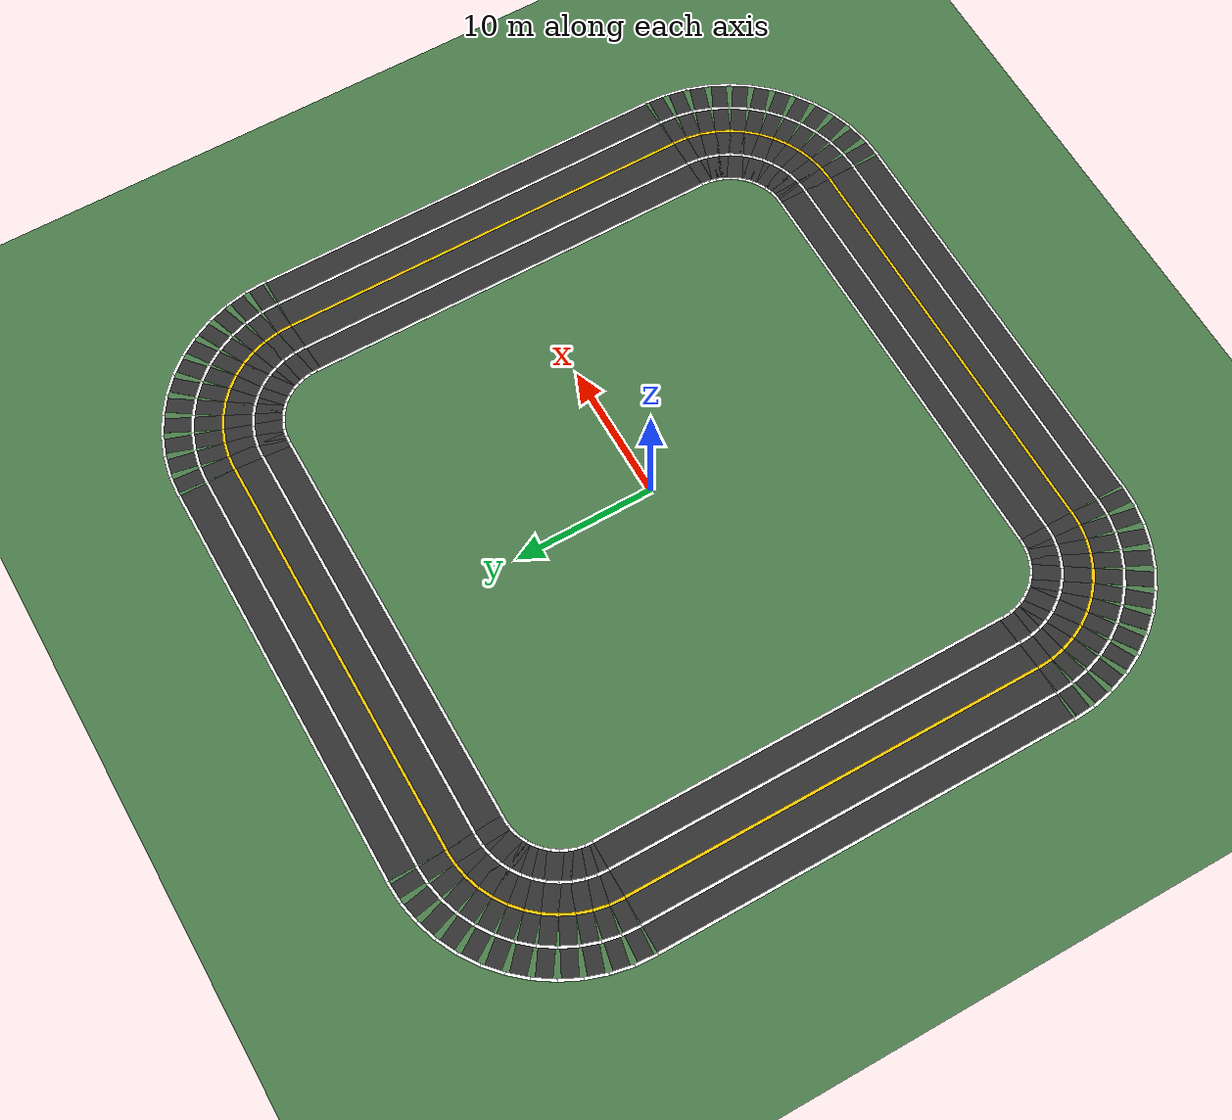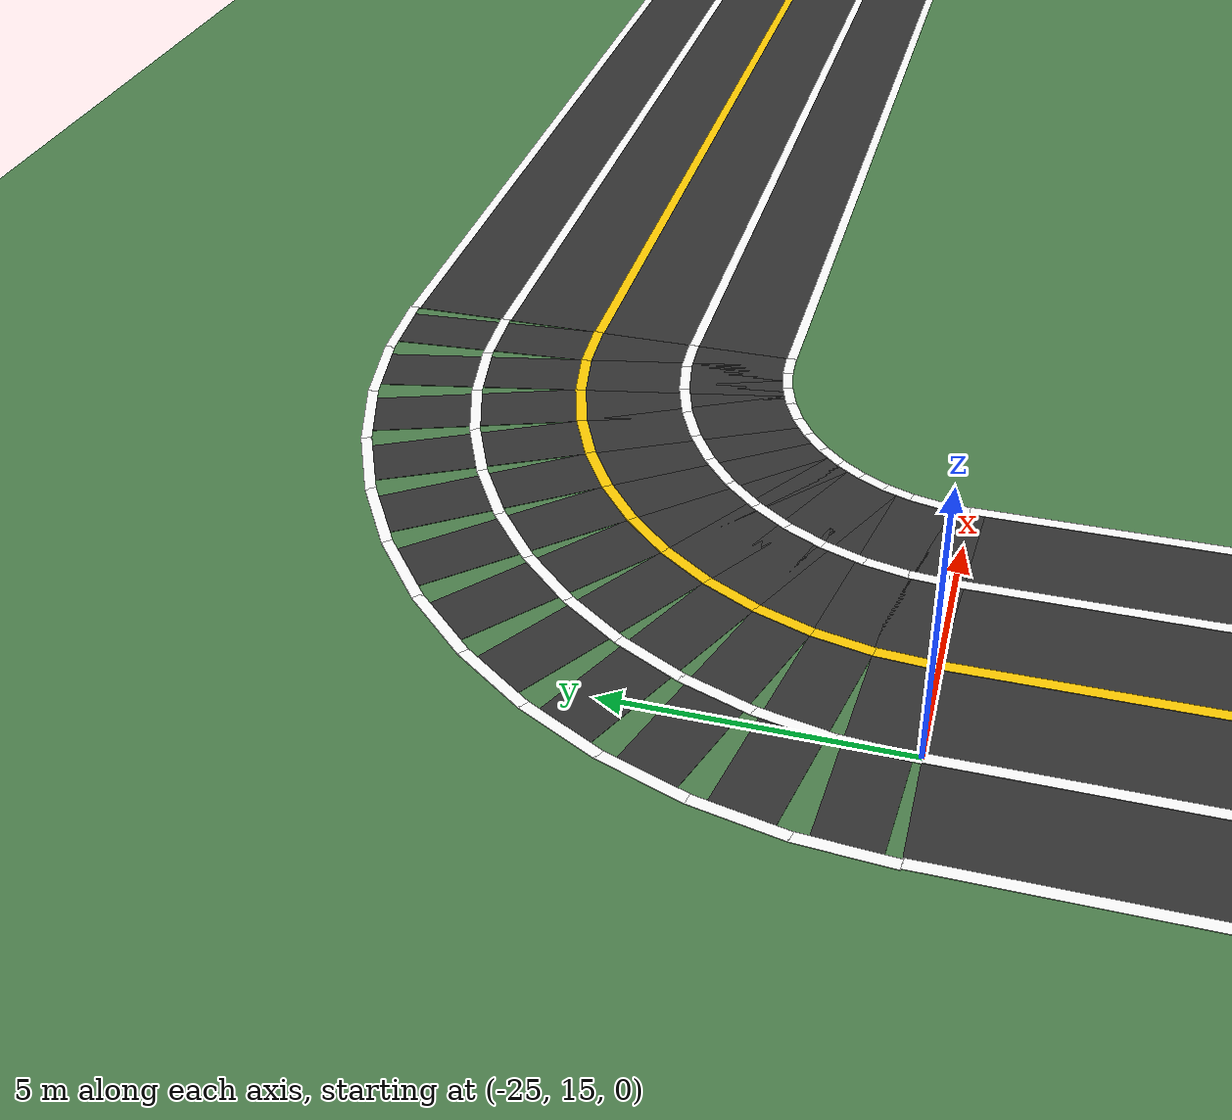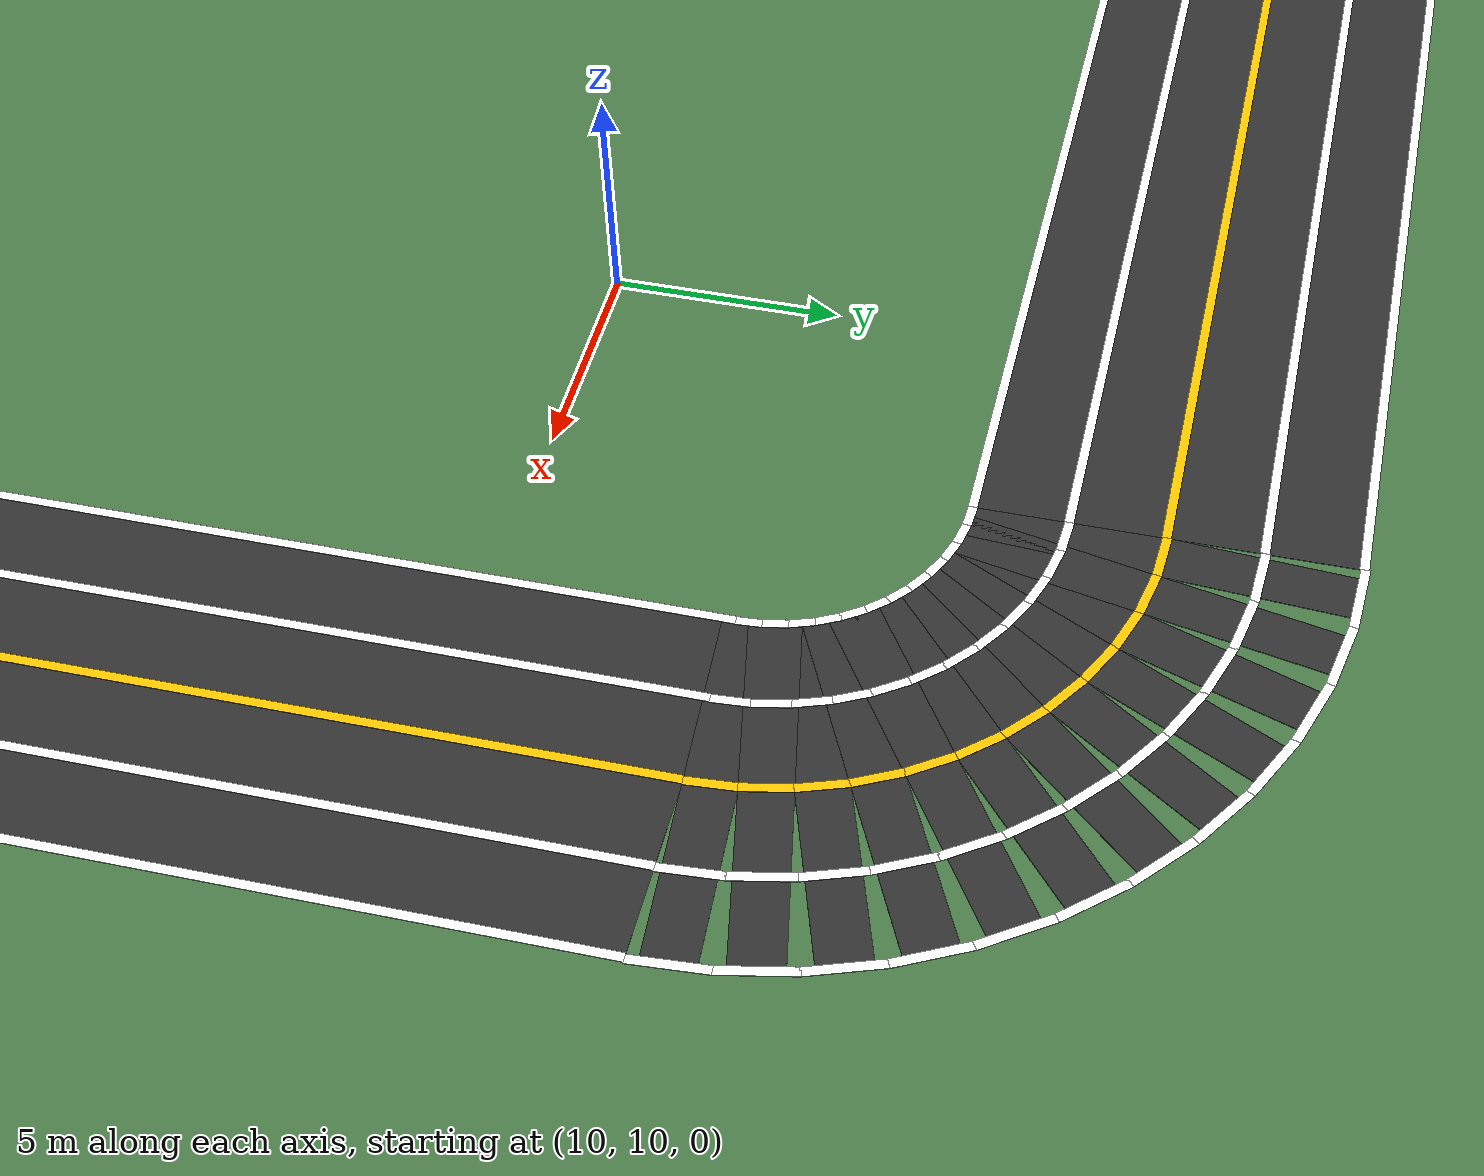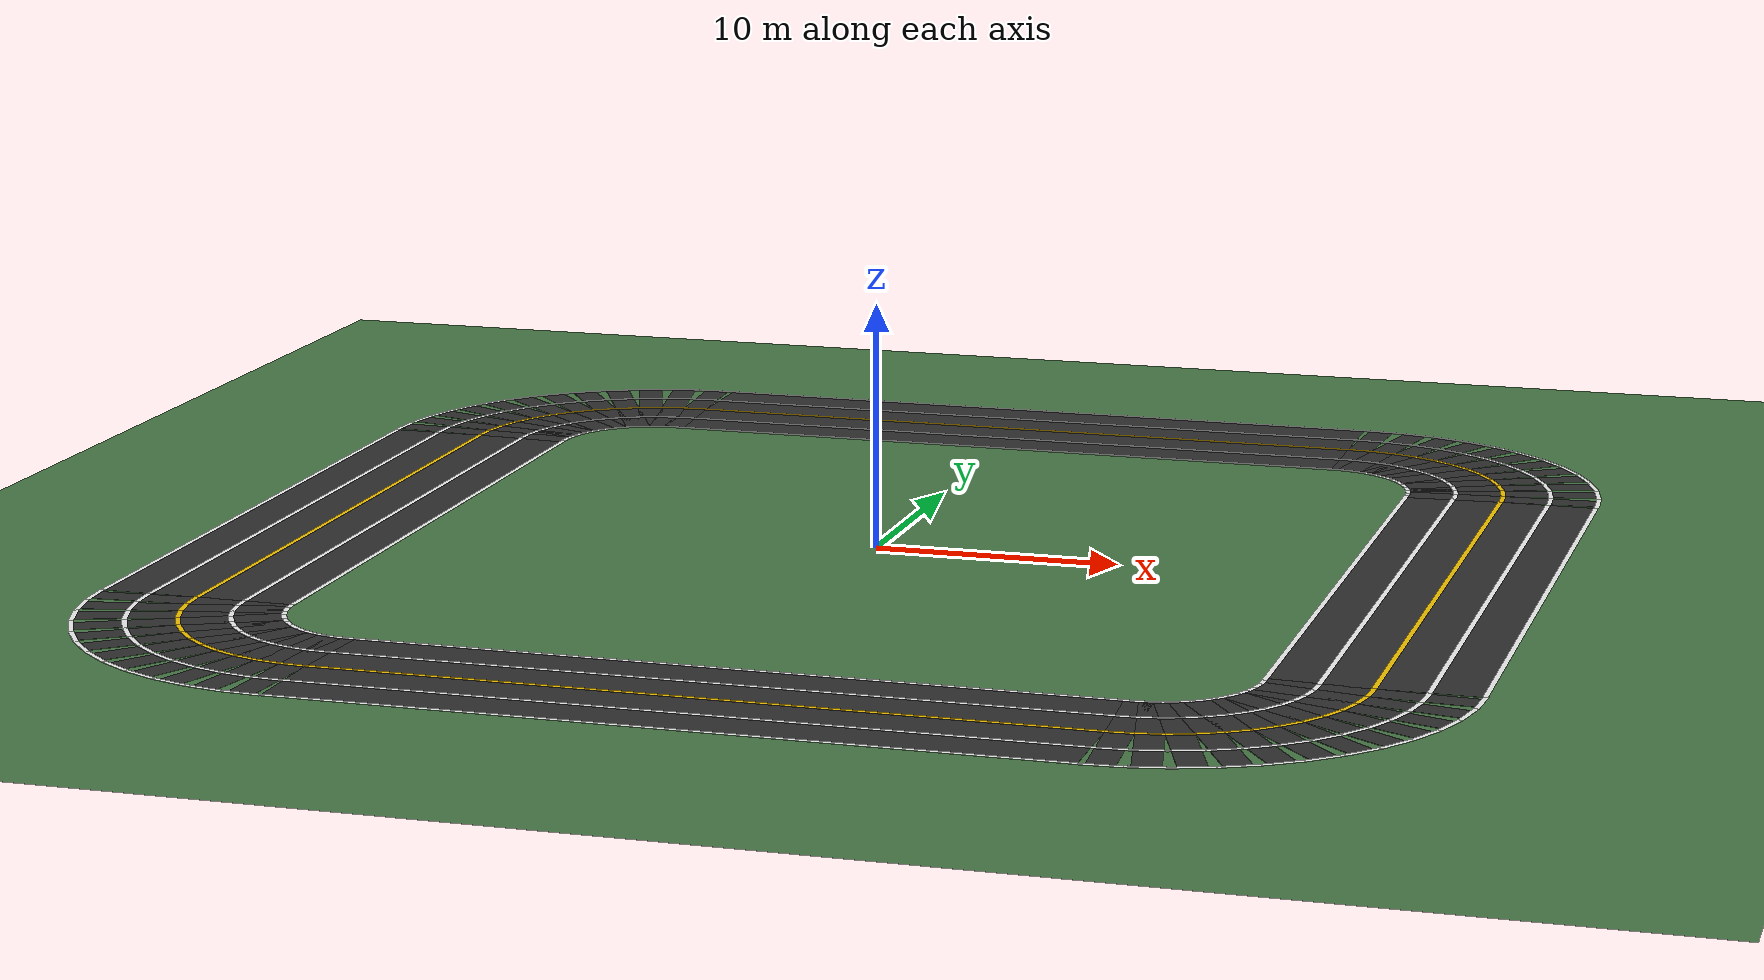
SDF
<?xml version="1.0" ?>
<sdf version="1.8">
  <world name="control_world">
    <!-- Modern Gazebo 필수 플러그인 -->
    <plugin filename="gz-sim-physics-system" name="gz::sim::systems::Physics"></plugin>
    <plugin filename="gz-sim-user-commands-system" name="gz::sim::systems::UserCommands"></plugin>
    <plugin filename="gz-sim-scene-broadcaster-system" name="gz::sim::systems::SceneBroadcaster"></plugin>
    <plugin filename="gz-sim-sensors-system" name="gz::sim::systems::Sensors">
      <render_engine>ogre2</render_engine>
    </plugin>
    <!-- 태양광 조명 -->
    <light type="directional" name="sun">
      <cast_shadows>true</cast_shadows>
      <pose>0 0 10 0 0 0</pose>
      <diffuse>0.8 0.8 0.8 1</diffuse>
      <specular>0.2 0.2 0.2 1</specular>
      <direction>-0.5 0.1 -0.9</direction>
    </light>

    <!-- 바닥 (잔디밭) -->
    <model name="ground_plane">
      <static>true</static>
      <link name="link">
        <collision name="collision">
          <geometry><plane><normal>0 0 1</normal><size>120 120</size></plane></geometry>
        </collision>
        <visual name="visual">
          <geometry><plane><normal>0 0 1</normal><size>120 120</size></plane></geometry>
          <material>
            <ambient>0.3 0.5 0.3 1</ambient>
            <diffuse>0.3 0.5 0.3 1</diffuse>
          </material>
        </visual>
      </link>
    </model>

    <!-- 왕복 4차선 둥근 사각형 트랙 -->
    <model name="rounded_rect_track">
      <static>true</static>
      <link name="track_link">

        <visual name="asphalt_0">
          <pose>0.0000 23.0000 0.0100 0 0 0.0000</pose>
          <geometry><box><size>30.0000 8.0000 0.01</size></box></geometry>
          <material><ambient>0.2 0.2 0.2 1</ambient><diffuse>0.2 0.2 0.2 1</diffuse></material>
        </visual>
        <visual name="asphalt_1">
          <pose>0.0000 -23.0000 0.0100 0 0 0.0000</pose>
          <geometry><box><size>30.0000 8.0000 0.01</size></box></geometry>
          <material><ambient>0.2 0.2 0.2 1</ambient><diffuse>0.2 0.2 0.2 1</diffuse></material>
        </visual>
        <visual name="asphalt_2">
          <pose>23.0000 0.0000 0.0100 0 0 1.5708</pose>
          <geometry><box><size>30.0000 8.0000 0.01</size></box></geometry>
          <material><ambient>0.2 0.2 0.2 1</ambient><diffuse>0.2 0.2 0.2 1</diffuse></material>
        </visual>
        <visual name="asphalt_3">
          <pose>-23.0000 0.0000 0.0100 0 0 1.5708</pose>
          <geometry><box><size>30.0000 8.0000 0.01</size></box></geometry>
          <material><ambient>0.2 0.2 0.2 1</ambient><diffuse>0.2 0.2 0.2 1</diffuse></material>
        </visual>
        <visual name="yellow_c_4">
          <pose>0.0000 23.0000 0.0200 0 0 0.0000</pose>
          <geometry><box><size>30.0000 0.2000 0.01</size></box></geometry>
          <material><ambient>1.0 0.8 0.0 1</ambient><diffuse>1.0 0.8 0.0 1</diffuse></material>
        </visual>
        <visual name="yellow_c_5">
          <pose>0.0000 -23.0000 0.0200 0 0 0.0000</pose>
          <geometry><box><size>30.0000 0.2000 0.01</size></box></geometry>
          <material><ambient>1.0 0.8 0.0 1</ambient><diffuse>1.0 0.8 0.0 1</diffuse></material>
        </visual>
        <visual name="yellow_c_6">
          <pose>23.0000 0.0000 0.0200 0 0 1.5708</pose>
          <geometry><box><size>30.0000 0.2000 0.01</size></box></geometry>
          <material><ambient>1.0 0.8 0.0 1</ambient><diffuse>1.0 0.8 0.0 1</diffuse></material>
        </visual>
        <visual name="yellow_c_7">
          <pose>-23.0000 0.0000 0.0200 0 0 1.5708</pose>
          <geometry><box><size>30.0000 0.2000 0.01</size></box></geometry>
          <material><ambient>1.0 0.8 0.0 1</ambient><diffuse>1.0 0.8 0.0 1</diffuse></material>
        </visual>
        <visual name="white_in_L_8">
          <pose>0.0000 25.0000 0.0200 0 0 0.0000</pose>
          <geometry><box><size>30.0000 0.2000 0.01</size></box></geometry>
          <material><ambient>1.0 1.0 1.0 1</ambient><diffuse>1.0 1.0 1.0 1</diffuse></material>
        </visual>
        <visual name="white_in_L_9">
          <pose>0.0000 -25.0000 0.0200 0 0 0.0000</pose>
          <geometry><box><size>30.0000 0.2000 0.01</size></box></geometry>
          <material><ambient>1.0 1.0 1.0 1</ambient><diffuse>1.0 1.0 1.0 1</diffuse></material>
        </visual>
        <visual name="white_in_L_10">
          <pose>25.0000 0.0000 0.0200 0 0 1.5708</pose>
          <geometry><box><size>30.0000 0.2000 0.01</size></box></geometry>
          <material><ambient>1.0 1.0 1.0 1</ambient><diffuse>1.0 1.0 1.0 1</diffuse></material>
        </visual>
        <visual name="white_in_L_11">
          <pose>-25.0000 0.0000 0.0200 0 0 1.5708</pose>
          <geometry><box><size>30.0000 0.2000 0.01</size></box></geometry>
          <material><ambient>1.0 1.0 1.0 1</ambient><diffuse>1.0 1.0 1.0 1</diffuse></material>
        </visual>
        <visual name="white_in_R_12">
          <pose>0.0000 21.0000 0.0200 0 0 0.0000</pose>
          <geometry><box><size>30.0000 0.2000 0.01</size></box></geometry>
          <material><ambient>1.0 1.0 1.0 1</ambient><diffuse>1.0 1.0 1.0 1</diffuse></material>
        </visual>
        <visual name="white_in_R_13">
          <pose>0.0000 -21.0000 0.0200 0 0 0.0000</pose>
          <geometry><box><size>30.0000 0.2000 0.01</size></box></geometry>
          <material><ambient>1.0 1.0 1.0 1</ambient><diffuse>1.0 1.0 1.0 1</diffuse></material>
        </visual>
        <visual name="white_in_R_14">
          <pose>21.0000 0.0000 0.0200 0 0 1.5708</pose>
          <geometry><box><size>30.0000 0.2000 0.01</size></box></geometry>
          <material><ambient>1.0 1.0 1.0 1</ambient><diffuse>1.0 1.0 1.0 1</diffuse></material>
        </visual>
        <visual name="white_in_R_15">
          <pose>-21.0000 0.0000 0.0200 0 0 1.5708</pose>
          <geometry><box><size>30.0000 0.2000 0.01</size></box></geometry>
          <material><ambient>1.0 1.0 1.0 1</ambient><diffuse>1.0 1.0 1.0 1</diffuse></material>
        </visual>
        <visual name="white_out_L_16">
          <pose>0.0000 27.0000 0.0200 0 0 0.0000</pose>
          <geometry><box><size>30.0000 0.2000 0.01</size></box></geometry>
          <material><ambient>1.0 1.0 1.0 1</ambient><diffuse>1.0 1.0 1.0 1</diffuse></material>
        </visual>
        <visual name="white_out_L_17">
          <pose>0.0000 -27.0000 0.0200 0 0 0.0000</pose>
          <geometry><box><size>30.0000 0.2000 0.01</size></box></geometry>
          <material><ambient>1.0 1.0 1.0 1</ambient><diffuse>1.0 1.0 1.0 1</diffuse></material>
        </visual>
        <visual name="white_out_L_18">
          <pose>27.0000 0.0000 0.0200 0 0 1.5708</pose>
          <geometry><box><size>30.0000 0.2000 0.01</size></box></geometry>
          <material><ambient>1.0 1.0 1.0 1</ambient><diffuse>1.0 1.0 1.0 1</diffuse></material>
        </visual>
        <visual name="white_out_L_19">
          <pose>-27.0000 0.0000 0.0200 0 0 1.5708</pose>
          <geometry><box><size>30.0000 0.2000 0.01</size></box></geometry>
          <material><ambient>1.0 1.0 1.0 1</ambient><diffuse>1.0 1.0 1.0 1</diffuse></material>
        </visual>
        <visual name="white_out_R_20">
          <pose>0.0000 19.0000 0.0200 0 0 0.0000</pose>
          <geometry><box><size>30.0000 0.2000 0.01</size></box></geometry>
          <material><ambient>1.0 1.0 1.0 1</ambient><diffuse>1.0 1.0 1.0 1</diffuse></material>
        </visual>
        <visual name="white_out_R_21">
          <pose>0.0000 -19.0000 0.0200 0 0 0.0000</pose>
          <geometry><box><size>30.0000 0.2000 0.01</size></box></geometry>
          <material><ambient>1.0 1.0 1.0 1</ambient><diffuse>1.0 1.0 1.0 1</diffuse></material>
        </visual>
        <visual name="white_out_R_22">
          <pose>19.0000 0.0000 0.0200 0 0 1.5708</pose>
          <geometry><box><size>30.0000 0.2000 0.01</size></box></geometry>
          <material><ambient>1.0 1.0 1.0 1</ambient><diffuse>1.0 1.0 1.0 1</diffuse></material>
        </visual>
        <visual name="white_out_R_23">
          <pose>-19.0000 0.0000 0.0200 0 0 1.5708</pose>
          <geometry><box><size>30.0000 0.2000 0.01</size></box></geometry>
          <material><ambient>1.0 1.0 1.0 1</ambient><diffuse>1.0 1.0 1.0 1</diffuse></material>
        </visual>
        <visual name="asphalt_24">
          <pose>22.9829 15.5232 0.0100 0 0 1.6362</pose>
          <geometry><box><size>1.0681 8.0000 0.01</size></box></geometry>
          <material><ambient>0.2 0.2 0.2 1</ambient><diffuse>0.2 0.2 0.2 1</diffuse></material>
        </visual>
        <visual name="yellow_c_25">
          <pose>22.9829 15.5232 0.0200 0 0 1.6362</pose>
          <geometry><box><size>1.0681 0.2000 0.01</size></box></geometry>
          <material><ambient>1.0 0.8 0.0 1</ambient><diffuse>1.0 0.8 0.0 1</diffuse></material>
        </visual>
        <visual name="white_in_L_26">
          <pose>24.9786 15.6540 0.0200 0 0 1.6362</pose>
          <geometry><box><size>1.3352 0.2000 0.01</size></box></geometry>
          <material><ambient>1.0 1.0 1.0 1</ambient><diffuse>1.0 1.0 1.0 1</diffuse></material>
        </visual>
        <visual name="white_in_R_27">
          <pose>20.9872 15.3924 0.0200 0 0 1.6362</pose>
          <geometry><box><size>0.8011 0.2000 0.01</size></box></geometry>
          <material><ambient>1.0 1.0 1.0 1</ambient><diffuse>1.0 1.0 1.0 1</diffuse></material>
        </visual>
        <visual name="white_out_L_28">
          <pose>26.9743 15.7848 0.0200 0 0 1.6362</pose>
          <geometry><box><size>1.6022 0.2000 0.01</size></box></geometry>
          <material><ambient>1.0 1.0 1.0 1</ambient><diffuse>1.0 1.0 1.0 1</diffuse></material>
        </visual>
        <visual name="white_out_R_29">
          <pose>18.9914 15.2616 0.0200 0 0 1.6362</pose>
          <geometry><box><size>0.5341 0.2000 0.01</size></box></geometry>
          <material><ambient>1.0 1.0 1.0 1</ambient><diffuse>1.0 1.0 1.0 1</diffuse></material>
        </visual>
        <visual name="asphalt_30">
          <pose>22.8463 16.5607 0.0100 0 0 1.7671</pose>
          <geometry><box><size>1.0681 8.0000 0.01</size></box></geometry>
          <material><ambient>0.2 0.2 0.2 1</ambient><diffuse>0.2 0.2 0.2 1</diffuse></material>
        </visual>
        <visual name="yellow_c_31">
          <pose>22.8463 16.5607 0.0200 0 0 1.7671</pose>
          <geometry><box><size>1.0681 0.2000 0.01</size></box></geometry>
          <material><ambient>1.0 0.8 0.0 1</ambient><diffuse>1.0 0.8 0.0 1</diffuse></material>
        </visual>
        <visual name="white_in_L_32">
          <pose>24.8079 16.9509 0.0200 0 0 1.7671</pose>
          <geometry><box><size>1.3352 0.2000 0.01</size></box></geometry>
          <material><ambient>1.0 1.0 1.0 1</ambient><diffuse>1.0 1.0 1.0 1</diffuse></material>
        </visual>
        <visual name="white_in_R_33">
          <pose>20.8847 16.1705 0.0200 0 0 1.7671</pose>
          <geometry><box><size>0.8011 0.2000 0.01</size></box></geometry>
          <material><ambient>1.0 1.0 1.0 1</ambient><diffuse>1.0 1.0 1.0 1</diffuse></material>
        </visual>
        <visual name="white_out_L_34">
          <pose>26.7694 17.3411 0.0200 0 0 1.7671</pose>
          <geometry><box><size>1.6022 0.2000 0.01</size></box></geometry>
          <material><ambient>1.0 1.0 1.0 1</ambient><diffuse>1.0 1.0 1.0 1</diffuse></material>
        </visual>
        <visual name="white_out_R_35">
          <pose>18.9231 15.7804 0.0200 0 0 1.7671</pose>
          <geometry><box><size>0.5341 0.2000 0.01</size></box></geometry>
          <material><ambient>1.0 1.0 1.0 1</ambient><diffuse>1.0 1.0 1.0 1</diffuse></material>
        </visual>
        <visual name="asphalt_36">
          <pose>22.5754 17.5715 0.0100 0 0 1.8980</pose>
          <geometry><box><size>1.0681 8.0000 0.01</size></box></geometry>
          <material><ambient>0.2 0.2 0.2 1</ambient><diffuse>0.2 0.2 0.2 1</diffuse></material>
        </visual>
        <visual name="yellow_c_37">
          <pose>22.5754 17.5715 0.0200 0 0 1.8980</pose>
          <geometry><box><size>1.0681 0.2000 0.01</size></box></geometry>
          <material><ambient>1.0 0.8 0.0 1</ambient><diffuse>1.0 0.8 0.0 1</diffuse></material>
        </visual>
        <visual name="white_in_L_38">
          <pose>24.4693 18.2144 0.0200 0 0 1.8980</pose>
          <geometry><box><size>1.3352 0.2000 0.01</size></box></geometry>
          <material><ambient>1.0 1.0 1.0 1</ambient><diffuse>1.0 1.0 1.0 1</diffuse></material>
        </visual>
        <visual name="white_in_R_39">
          <pose>20.6816 16.9286 0.0200 0 0 1.8980</pose>
          <geometry><box><size>0.8011 0.2000 0.01</size></box></geometry>
          <material><ambient>1.0 1.0 1.0 1</ambient><diffuse>1.0 1.0 1.0 1</diffuse></material>
        </visual>
        <visual name="white_out_L_40">
          <pose>26.3632 18.8573 0.0200 0 0 1.8980</pose>
          <geometry><box><size>1.6022 0.2000 0.01</size></box></geometry>
          <material><ambient>1.0 1.0 1.0 1</ambient><diffuse>1.0 1.0 1.0 1</diffuse></material>
        </visual>
        <visual name="white_out_R_41">
          <pose>18.7877 16.2858 0.0200 0 0 1.8980</pose>
          <geometry><box><size>0.5341 0.2000 0.01</size></box></geometry>
          <material><ambient>1.0 1.0 1.0 1</ambient><diffuse>1.0 1.0 1.0 1</diffuse></material>
        </visual>
        <visual name="asphalt_42">
          <pose>22.1750 18.5383 0.0100 0 0 2.0289</pose>
          <geometry><box><size>1.0681 8.0000 0.01</size></box></geometry>
          <material><ambient>0.2 0.2 0.2 1</ambient><diffuse>0.2 0.2 0.2 1</diffuse></material>
        </visual>
        <visual name="yellow_c_43">
          <pose>22.1750 18.5383 0.0200 0 0 2.0289</pose>
          <geometry><box><size>1.0681 0.2000 0.01</size></box></geometry>
          <material><ambient>1.0 0.8 0.0 1</ambient><diffuse>1.0 0.8 0.0 1</diffuse></material>
        </visual>
        <visual name="white_in_L_44">
          <pose>23.9687 19.4229 0.0200 0 0 2.0289</pose>
          <geometry><box><size>1.3352 0.2000 0.01</size></box></geometry>
          <material><ambient>1.0 1.0 1.0 1</ambient><diffuse>1.0 1.0 1.0 1</diffuse></material>
        </visual>
        <visual name="white_in_R_45">
          <pose>20.3812 17.6537 0.0200 0 0 2.0289</pose>
          <geometry><box><size>0.8011 0.2000 0.01</size></box></geometry>
          <material><ambient>1.0 1.0 1.0 1</ambient><diffuse>1.0 1.0 1.0 1</diffuse></material>
        </visual>
        <visual name="white_out_L_46">
          <pose>25.7625 20.3075 0.0200 0 0 2.0289</pose>
          <geometry><box><size>1.6022 0.2000 0.01</size></box></geometry>
          <material><ambient>1.0 1.0 1.0 1</ambient><diffuse>1.0 1.0 1.0 1</diffuse></material>
        </visual>
        <visual name="white_out_R_47">
          <pose>18.5875 16.7692 0.0200 0 0 2.0289</pose>
          <geometry><box><size>0.5341 0.2000 0.01</size></box></geometry>
          <material><ambient>1.0 1.0 1.0 1</ambient><diffuse>1.0 1.0 1.0 1</diffuse></material>
        </visual>
        <visual name="asphalt_48">
          <pose>21.6518 19.4446 0.0100 0 0 2.1598</pose>
          <geometry><box><size>1.0681 8.0000 0.01</size></box></geometry>
          <material><ambient>0.2 0.2 0.2 1</ambient><diffuse>0.2 0.2 0.2 1</diffuse></material>
        </visual>
        <visual name="yellow_c_49">
          <pose>21.6518 19.4446 0.0200 0 0 2.1598</pose>
          <geometry><box><size>1.0681 0.2000 0.01</size></box></geometry>
          <material><ambient>1.0 0.8 0.0 1</ambient><diffuse>1.0 0.8 0.0 1</diffuse></material>
        </visual>
        <visual name="white_in_L_50">
          <pose>23.3147 20.5557 0.0200 0 0 2.1598</pose>
          <geometry><box><size>1.3352 0.2000 0.01</size></box></geometry>
          <material><ambient>1.0 1.0 1.0 1</ambient><diffuse>1.0 1.0 1.0 1</diffuse></material>
        </visual>
        <visual name="white_in_R_51">
          <pose>19.9888 18.3334 0.0200 0 0 2.1598</pose>
          <geometry><box><size>0.8011 0.2000 0.01</size></box></geometry>
          <material><ambient>1.0 1.0 1.0 1</ambient><diffuse>1.0 1.0 1.0 1</diffuse></material>
        </visual>
        <visual name="white_out_L_52">
          <pose>24.9776 21.6668 0.0200 0 0 2.1598</pose>
          <geometry><box><size>1.6022 0.2000 0.01</size></box></geometry>
          <material><ambient>1.0 1.0 1.0 1</ambient><diffuse>1.0 1.0 1.0 1</diffuse></material>
        </visual>
        <visual name="white_out_R_53">
          <pose>18.3259 17.2223 0.0200 0 0 2.1598</pose>
          <geometry><box><size>0.5341 0.2000 0.01</size></box></geometry>
          <material><ambient>1.0 1.0 1.0 1</ambient><diffuse>1.0 1.0 1.0 1</diffuse></material>
        </visual>
        <visual name="asphalt_54">
          <pose>21.0147 20.2748 0.0100 0 0 2.2907</pose>
          <geometry><box><size>1.0681 8.0000 0.01</size></box></geometry>
          <material><ambient>0.2 0.2 0.2 1</ambient><diffuse>0.2 0.2 0.2 1</diffuse></material>
        </visual>
        <visual name="yellow_c_55">
          <pose>21.0147 20.2748 0.0200 0 0 2.2907</pose>
          <geometry><box><size>1.0681 0.2000 0.01</size></box></geometry>
          <material><ambient>1.0 0.8 0.0 1</ambient><diffuse>1.0 0.8 0.0 1</diffuse></material>
        </visual>
        <visual name="white_in_L_56">
          <pose>22.5184 21.5935 0.0200 0 0 2.2907</pose>
          <geometry><box><size>1.3352 0.2000 0.01</size></box></geometry>
          <material><ambient>1.0 1.0 1.0 1</ambient><diffuse>1.0 1.0 1.0 1</diffuse></material>
        </visual>
        <visual name="white_in_R_57">
          <pose>19.5110 18.9561 0.0200 0 0 2.2907</pose>
          <geometry><box><size>0.8011 0.2000 0.01</size></box></geometry>
          <material><ambient>1.0 1.0 1.0 1</ambient><diffuse>1.0 1.0 1.0 1</diffuse></material>
        </visual>
        <visual name="white_out_L_58">
          <pose>24.0221 22.9121 0.0200 0 0 2.2907</pose>
          <geometry><box><size>1.6022 0.2000 0.01</size></box></geometry>
          <material><ambient>1.0 1.0 1.0 1</ambient><diffuse>1.0 1.0 1.0 1</diffuse></material>
        </visual>
        <visual name="white_out_R_59">
          <pose>18.0074 17.6374 0.0200 0 0 2.2907</pose>
          <geometry><box><size>0.5341 0.2000 0.01</size></box></geometry>
          <material><ambient>1.0 1.0 1.0 1</ambient><diffuse>1.0 1.0 1.0 1</diffuse></material>
        </visual>
        <visual name="asphalt_60">
          <pose>20.2748 21.0147 0.0100 0 0 2.4216</pose>
          <geometry><box><size>1.0681 8.0000 0.01</size></box></geometry>
          <material><ambient>0.2 0.2 0.2 1</ambient><diffuse>0.2 0.2 0.2 1</diffuse></material>
        </visual>
        <visual name="yellow_c_61">
          <pose>20.2748 21.0147 0.0200 0 0 2.4216</pose>
          <geometry><box><size>1.0681 0.2000 0.01</size></box></geometry>
          <material><ambient>1.0 0.8 0.0 1</ambient><diffuse>1.0 0.8 0.0 1</diffuse></material>
        </visual>
        <visual name="white_in_L_62">
          <pose>21.5935 22.5184 0.0200 0 0 2.4216</pose>
          <geometry><box><size>1.3352 0.2000 0.01</size></box></geometry>
          <material><ambient>1.0 1.0 1.0 1</ambient><diffuse>1.0 1.0 1.0 1</diffuse></material>
        </visual>
        <visual name="white_in_R_63">
          <pose>18.9561 19.5110 0.0200 0 0 2.4216</pose>
          <geometry><box><size>0.8011 0.2000 0.01</size></box></geometry>
          <material><ambient>1.0 1.0 1.0 1</ambient><diffuse>1.0 1.0 1.0 1</diffuse></material>
        </visual>
        <visual name="white_out_L_64">
          <pose>22.9121 24.0221 0.0200 0 0 2.4216</pose>
          <geometry><box><size>1.6022 0.2000 0.01</size></box></geometry>
          <material><ambient>1.0 1.0 1.0 1</ambient><diffuse>1.0 1.0 1.0 1</diffuse></material>
        </visual>
        <visual name="white_out_R_65">
          <pose>17.6374 18.0074 0.0200 0 0 2.4216</pose>
          <geometry><box><size>0.5341 0.2000 0.01</size></box></geometry>
          <material><ambient>1.0 1.0 1.0 1</ambient><diffuse>1.0 1.0 1.0 1</diffuse></material>
        </visual>
        <visual name="asphalt_66">
          <pose>19.4446 21.6518 0.0100 0 0 2.5525</pose>
          <geometry><box><size>1.0681 8.0000 0.01</size></box></geometry>
          <material><ambient>0.2 0.2 0.2 1</ambient><diffuse>0.2 0.2 0.2 1</diffuse></material>
        </visual>
        <visual name="yellow_c_67">
          <pose>19.4446 21.6518 0.0200 0 0 2.5525</pose>
          <geometry><box><size>1.0681 0.2000 0.01</size></box></geometry>
          <material><ambient>1.0 0.8 0.0 1</ambient><diffuse>1.0 0.8 0.0 1</diffuse></material>
        </visual>
        <visual name="white_in_L_68">
          <pose>20.5557 23.3147 0.0200 0 0 2.5525</pose>
          <geometry><box><size>1.3352 0.2000 0.01</size></box></geometry>
          <material><ambient>1.0 1.0 1.0 1</ambient><diffuse>1.0 1.0 1.0 1</diffuse></material>
        </visual>
        <visual name="white_in_R_69">
          <pose>18.3334 19.9888 0.0200 0 0 2.5525</pose>
          <geometry><box><size>0.8011 0.2000 0.01</size></box></geometry>
          <material><ambient>1.0 1.0 1.0 1</ambient><diffuse>1.0 1.0 1.0 1</diffuse></material>
        </visual>
        <visual name="white_out_L_70">
          <pose>21.6668 24.9776 0.0200 0 0 2.5525</pose>
          <geometry><box><size>1.6022 0.2000 0.01</size></box></geometry>
          <material><ambient>1.0 1.0 1.0 1</ambient><diffuse>1.0 1.0 1.0 1</diffuse></material>
        </visual>
        <visual name="white_out_R_71">
          <pose>17.2223 18.3259 0.0200 0 0 2.5525</pose>
          <geometry><box><size>0.5341 0.2000 0.01</size></box></geometry>
          <material><ambient>1.0 1.0 1.0 1</ambient><diffuse>1.0 1.0 1.0 1</diffuse></material>
        </visual>
        <visual name="asphalt_72">
          <pose>18.5383 22.1750 0.0100 0 0 2.6834</pose>
          <geometry><box><size>1.0681 8.0000 0.01</size></box></geometry>
          <material><ambient>0.2 0.2 0.2 1</ambient><diffuse>0.2 0.2 0.2 1</diffuse></material>
        </visual>
        <visual name="yellow_c_73">
          <pose>18.5383 22.1750 0.0200 0 0 2.6834</pose>
          <geometry><box><size>1.0681 0.2000 0.01</size></box></geometry>
          <material><ambient>1.0 0.8 0.0 1</ambient><diffuse>1.0 0.8 0.0 1</diffuse></material>
        </visual>
        <visual name="white_in_L_74">
          <pose>19.4229 23.9687 0.0200 0 0 2.6834</pose>
          <geometry><box><size>1.3352 0.2000 0.01</size></box></geometry>
          <material><ambient>1.0 1.0 1.0 1</ambient><diffuse>1.0 1.0 1.0 1</diffuse></material>
        </visual>
        <visual name="white_in_R_75">
          <pose>17.6537 20.3812 0.0200 0 0 2.6834</pose>
          <geometry><box><size>0.8011 0.2000 0.01</size></box></geometry>
          <material><ambient>1.0 1.0 1.0 1</ambient><diffuse>1.0 1.0 1.0 1</diffuse></material>
        </visual>
        <visual name="white_out_L_76">
          <pose>20.3075 25.7625 0.0200 0 0 2.6834</pose>
          <geometry><box><size>1.6022 0.2000 0.01</size></box></geometry>
          <material><ambient>1.0 1.0 1.0 1</ambient><diffuse>1.0 1.0 1.0 1</diffuse></material>
        </visual>
        <visual name="white_out_R_77">
          <pose>16.7692 18.5875 0.0200 0 0 2.6834</pose>
          <geometry><box><size>0.5341 0.2000 0.01</size></box></geometry>
          <material><ambient>1.0 1.0 1.0 1</ambient><diffuse>1.0 1.0 1.0 1</diffuse></material>
        </visual>
        <visual name="asphalt_78">
          <pose>17.5715 22.5754 0.0100 0 0 2.8143</pose>
          <geometry><box><size>1.0681 8.0000 0.01</size></box></geometry>
          <material><ambient>0.2 0.2 0.2 1</ambient><diffuse>0.2 0.2 0.2 1</diffuse></material>
        </visual>
        <visual name="yellow_c_79">
          <pose>17.5715 22.5754 0.0200 0 0 2.8143</pose>
          <geometry><box><size>1.0681 0.2000 0.01</size></box></geometry>
          <material><ambient>1.0 0.8 0.0 1</ambient><diffuse>1.0 0.8 0.0 1</diffuse></material>
        </visual>
        <visual name="white_in_L_80">
          <pose>18.2144 24.4693 0.0200 0 0 2.8143</pose>
          <geometry><box><size>1.3352 0.2000 0.01</size></box></geometry>
          <material><ambient>1.0 1.0 1.0 1</ambient><diffuse>1.0 1.0 1.0 1</diffuse></material>
        </visual>
        <visual name="white_in_R_81">
          <pose>16.9286 20.6816 0.0200 0 0 2.8143</pose>
          <geometry><box><size>0.8011 0.2000 0.01</size></box></geometry>
          <material><ambient>1.0 1.0 1.0 1</ambient><diffuse>1.0 1.0 1.0 1</diffuse></material>
        </visual>
        <visual name="white_out_L_82">
          <pose>18.8573 26.3632 0.0200 0 0 2.8143</pose>
          <geometry><box><size>1.6022 0.2000 0.01</size></box></geometry>
          <material><ambient>1.0 1.0 1.0 1</ambient><diffuse>1.0 1.0 1.0 1</diffuse></material>
        </visual>
        <visual name="white_out_R_83">
          <pose>16.2858 18.7877 0.0200 0 0 2.8143</pose>
          <geometry><box><size>0.5341 0.2000 0.01</size></box></geometry>
          <material><ambient>1.0 1.0 1.0 1</ambient><diffuse>1.0 1.0 1.0 1</diffuse></material>
        </visual>
        <visual name="asphalt_84">
          <pose>16.5607 22.8463 0.0100 0 0 2.9452</pose>
          <geometry><box><size>1.0681 8.0000 0.01</size></box></geometry>
          <material><ambient>0.2 0.2 0.2 1</ambient><diffuse>0.2 0.2 0.2 1</diffuse></material>
        </visual>
        <visual name="yellow_c_85">
          <pose>16.5607 22.8463 0.0200 0 0 2.9452</pose>
          <geometry><box><size>1.0681 0.2000 0.01</size></box></geometry>
          <material><ambient>1.0 0.8 0.0 1</ambient><diffuse>1.0 0.8 0.0 1</diffuse></material>
        </visual>
        <visual name="white_in_L_86">
          <pose>16.9509 24.8079 0.0200 0 0 2.9452</pose>
          <geometry><box><size>1.3352 0.2000 0.01</size></box></geometry>
          <material><ambient>1.0 1.0 1.0 1</ambient><diffuse>1.0 1.0 1.0 1</diffuse></material>
        </visual>
        <visual name="white_in_R_87">
          <pose>16.1705 20.8847 0.0200 0 0 2.9452</pose>
          <geometry><box><size>0.8011 0.2000 0.01</size></box></geometry>
          <material><ambient>1.0 1.0 1.0 1</ambient><diffuse>1.0 1.0 1.0 1</diffuse></material>
        </visual>
        <visual name="white_out_L_88">
          <pose>17.3411 26.7694 0.0200 0 0 2.9452</pose>
          <geometry><box><size>1.6022 0.2000 0.01</size></box></geometry>
          <material><ambient>1.0 1.0 1.0 1</ambient><diffuse>1.0 1.0 1.0 1</diffuse></material>
        </visual>
        <visual name="white_out_R_89">
          <pose>15.7804 18.9231 0.0200 0 0 2.9452</pose>
          <geometry><box><size>0.5341 0.2000 0.01</size></box></geometry>
          <material><ambient>1.0 1.0 1.0 1</ambient><diffuse>1.0 1.0 1.0 1</diffuse></material>
        </visual>
        <visual name="asphalt_90">
          <pose>15.5232 22.9829 0.0100 0 0 3.0761</pose>
          <geometry><box><size>1.0681 8.0000 0.01</size></box></geometry>
          <material><ambient>0.2 0.2 0.2 1</ambient><diffuse>0.2 0.2 0.2 1</diffuse></material>
        </visual>
        <visual name="yellow_c_91">
          <pose>15.5232 22.9829 0.0200 0 0 3.0761</pose>
          <geometry><box><size>1.0681 0.2000 0.01</size></box></geometry>
          <material><ambient>1.0 0.8 0.0 1</ambient><diffuse>1.0 0.8 0.0 1</diffuse></material>
        </visual>
        <visual name="white_in_L_92">
          <pose>15.6540 24.9786 0.0200 0 0 3.0761</pose>
          <geometry><box><size>1.3352 0.2000 0.01</size></box></geometry>
          <material><ambient>1.0 1.0 1.0 1</ambient><diffuse>1.0 1.0 1.0 1</diffuse></material>
        </visual>
        <visual name="white_in_R_93">
          <pose>15.3924 20.9872 0.0200 0 0 3.0761</pose>
          <geometry><box><size>0.8011 0.2000 0.01</size></box></geometry>
          <material><ambient>1.0 1.0 1.0 1</ambient><diffuse>1.0 1.0 1.0 1</diffuse></material>
        </visual>
        <visual name="white_out_L_94">
          <pose>15.7848 26.9743 0.0200 0 0 3.0761</pose>
          <geometry><box><size>1.6022 0.2000 0.01</size></box></geometry>
          <material><ambient>1.0 1.0 1.0 1</ambient><diffuse>1.0 1.0 1.0 1</diffuse></material>
        </visual>
        <visual name="white_out_R_95">
          <pose>15.2616 18.9914 0.0200 0 0 3.0761</pose>
          <geometry><box><size>0.5341 0.2000 0.01</size></box></geometry>
          <material><ambient>1.0 1.0 1.0 1</ambient><diffuse>1.0 1.0 1.0 1</diffuse></material>
        </visual>
        <visual name="asphalt_96">
          <pose>-15.5232 22.9829 0.0100 0 0 3.2070</pose>
          <geometry><box><size>1.0681 8.0000 0.01</size></box></geometry>
          <material><ambient>0.2 0.2 0.2 1</ambient><diffuse>0.2 0.2 0.2 1</diffuse></material>
        </visual>
        <visual name="yellow_c_97">
          <pose>-15.5232 22.9829 0.0200 0 0 3.2070</pose>
          <geometry><box><size>1.0681 0.2000 0.01</size></box></geometry>
          <material><ambient>1.0 0.8 0.0 1</ambient><diffuse>1.0 0.8 0.0 1</diffuse></material>
        </visual>
        <visual name="white_in_L_98">
          <pose>-15.6540 24.9786 0.0200 0 0 3.2070</pose>
          <geometry><box><size>1.3352 0.2000 0.01</size></box></geometry>
          <material><ambient>1.0 1.0 1.0 1</ambient><diffuse>1.0 1.0 1.0 1</diffuse></material>
        </visual>
        <visual name="white_in_R_99">
          <pose>-15.3924 20.9872 0.0200 0 0 3.2070</pose>
          <geometry><box><size>0.8011 0.2000 0.01</size></box></geometry>
          <material><ambient>1.0 1.0 1.0 1</ambient><diffuse>1.0 1.0 1.0 1</diffuse></material>
        </visual>
        <visual name="white_out_L_100">
          <pose>-15.7848 26.9743 0.0200 0 0 3.2070</pose>
          <geometry><box><size>1.6022 0.2000 0.01</size></box></geometry>
          <material><ambient>1.0 1.0 1.0 1</ambient><diffuse>1.0 1.0 1.0 1</diffuse></material>
        </visual>
        <visual name="white_out_R_101">
          <pose>-15.2616 18.9914 0.0200 0 0 3.2070</pose>
          <geometry><box><size>0.5341 0.2000 0.01</size></box></geometry>
          <material><ambient>1.0 1.0 1.0 1</ambient><diffuse>1.0 1.0 1.0 1</diffuse></material>
        </visual>
        <visual name="asphalt_102">
          <pose>-16.5607 22.8463 0.0100 0 0 3.3379</pose>
          <geometry><box><size>1.0681 8.0000 0.01</size></box></geometry>
          <material><ambient>0.2 0.2 0.2 1</ambient><diffuse>0.2 0.2 0.2 1</diffuse></material>
        </visual>
        <visual name="yellow_c_103">
          <pose>-16.5607 22.8463 0.0200 0 0 3.3379</pose>
          <geometry><box><size>1.0681 0.2000 0.01</size></box></geometry>
          <material><ambient>1.0 0.8 0.0 1</ambient><diffuse>1.0 0.8 0.0 1</diffuse></material>
        </visual>
        <visual name="white_in_L_104">
          <pose>-16.9509 24.8079 0.0200 0 0 3.3379</pose>
          <geometry><box><size>1.3352 0.2000 0.01</size></box></geometry>
          <material><ambient>1.0 1.0 1.0 1</ambient><diffuse>1.0 1.0 1.0 1</diffuse></material>
        </visual>
        <visual name="white_in_R_105">
          <pose>-16.1705 20.8847 0.0200 0 0 3.3379</pose>
          <geometry><box><size>0.8011 0.2000 0.01</size></box></geometry>
          <material><ambient>1.0 1.0 1.0 1</ambient><diffuse>1.0 1.0 1.0 1</diffuse></material>
        </visual>
        <visual name="white_out_L_106">
          <pose>-17.3411 26.7694 0.0200 0 0 3.3379</pose>
          <geometry><box><size>1.6022 0.2000 0.01</size></box></geometry>
          <material><ambient>1.0 1.0 1.0 1</ambient><diffuse>1.0 1.0 1.0 1</diffuse></material>
        </visual>
        <visual name="white_out_R_107">
          <pose>-15.7804 18.9231 0.0200 0 0 3.3379</pose>
          <geometry><box><size>0.5341 0.2000 0.01</size></box></geometry>
          <material><ambient>1.0 1.0 1.0 1</ambient><diffuse>1.0 1.0 1.0 1</diffuse></material>
        </visual>
        <visual name="asphalt_108">
          <pose>-17.5715 22.5754 0.0100 0 0 3.4688</pose>
          <geometry><box><size>1.0681 8.0000 0.01</size></box></geometry>
          <material><ambient>0.2 0.2 0.2 1</ambient><diffuse>0.2 0.2 0.2 1</diffuse></material>
        </visual>
        <visual name="yellow_c_109">
          <pose>-17.5715 22.5754 0.0200 0 0 3.4688</pose>
          <geometry><box><size>1.0681 0.2000 0.01</size></box></geometry>
          <material><ambient>1.0 0.8 0.0 1</ambient><diffuse>1.0 0.8 0.0 1</diffuse></material>
        </visual>
        <visual name="white_in_L_110">
          <pose>-18.2144 24.4693 0.0200 0 0 3.4688</pose>
          <geometry><box><size>1.3352 0.2000 0.01</size></box></geometry>
          <material><ambient>1.0 1.0 1.0 1</ambient><diffuse>1.0 1.0 1.0 1</diffuse></material>
        </visual>
        <visual name="white_in_R_111">
          <pose>-16.9286 20.6816 0.0200 0 0 3.4688</pose>
          <geometry><box><size>0.8011 0.2000 0.01</size></box></geometry>
          <material><ambient>1.0 1.0 1.0 1</ambient><diffuse>1.0 1.0 1.0 1</diffuse></material>
        </visual>
        <visual name="white_out_L_112">
          <pose>-18.8573 26.3632 0.0200 0 0 3.4688</pose>
          <geometry><box><size>1.6022 0.2000 0.01</size></box></geometry>
          <material><ambient>1.0 1.0 1.0 1</ambient><diffuse>1.0 1.0 1.0 1</diffuse></material>
        </visual>
        <visual name="white_out_R_113">
          <pose>-16.2858 18.7877 0.0200 0 0 3.4688</pose>
          <geometry><box><size>0.5341 0.2000 0.01</size></box></geometry>
          <material><ambient>1.0 1.0 1.0 1</ambient><diffuse>1.0 1.0 1.0 1</diffuse></material>
        </visual>
        <visual name="asphalt_114">
          <pose>-18.5383 22.1750 0.0100 0 0 3.5997</pose>
          <geometry><box><size>1.0681 8.0000 0.01</size></box></geometry>
          <material><ambient>0.2 0.2 0.2 1</ambient><diffuse>0.2 0.2 0.2 1</diffuse></material>
        </visual>
        <visual name="yellow_c_115">
          <pose>-18.5383 22.1750 0.0200 0 0 3.5997</pose>
          <geometry><box><size>1.0681 0.2000 0.01</size></box></geometry>
          <material><ambient>1.0 0.8 0.0 1</ambient><diffuse>1.0 0.8 0.0 1</diffuse></material>
        </visual>
        <visual name="white_in_L_116">
          <pose>-19.4229 23.9687 0.0200 0 0 3.5997</pose>
          <geometry><box><size>1.3352 0.2000 0.01</size></box></geometry>
          <material><ambient>1.0 1.0 1.0 1</ambient><diffuse>1.0 1.0 1.0 1</diffuse></material>
        </visual>
        <visual name="white_in_R_117">
          <pose>-17.6537 20.3812 0.0200 0 0 3.5997</pose>
          <geometry><box><size>0.8011 0.2000 0.01</size></box></geometry>
          <material><ambient>1.0 1.0 1.0 1</ambient><diffuse>1.0 1.0 1.0 1</diffuse></material>
        </visual>
        <visual name="white_out_L_118">
          <pose>-20.3075 25.7625 0.0200 0 0 3.5997</pose>
          <geometry><box><size>1.6022 0.2000 0.01</size></box></geometry>
          <material><ambient>1.0 1.0 1.0 1</ambient><diffuse>1.0 1.0 1.0 1</diffuse></material>
        </visual>
        <visual name="white_out_R_119">
          <pose>-16.7692 18.5875 0.0200 0 0 3.5997</pose>
          <geometry><box><size>0.5341 0.2000 0.01</size></box></geometry>
          <material><ambient>1.0 1.0 1.0 1</ambient><diffuse>1.0 1.0 1.0 1</diffuse></material>
        </visual>
        <visual name="asphalt_120">
          <pose>-19.4446 21.6518 0.0100 0 0 3.7306</pose>
          <geometry><box><size>1.0681 8.0000 0.01</size></box></geometry>
          <material><ambient>0.2 0.2 0.2 1</ambient><diffuse>0.2 0.2 0.2 1</diffuse></material>
        </visual>
        <visual name="yellow_c_121">
          <pose>-19.4446 21.6518 0.0200 0 0 3.7306</pose>
          <geometry><box><size>1.0681 0.2000 0.01</size></box></geometry>
          <material><ambient>1.0 0.8 0.0 1</ambient><diffuse>1.0 0.8 0.0 1</diffuse></material>
        </visual>
        <visual name="white_in_L_122">
          <pose>-20.5557 23.3147 0.0200 0 0 3.7306</pose>
          <geometry><box><size>1.3352 0.2000 0.01</size></box></geometry>
          <material><ambient>1.0 1.0 1.0 1</ambient><diffuse>1.0 1.0 1.0 1</diffuse></material>
        </visual>
        <visual name="white_in_R_123">
          <pose>-18.3334 19.9888 0.0200 0 0 3.7306</pose>
          <geometry><box><size>0.8011 0.2000 0.01</size></box></geometry>
          <material><ambient>1.0 1.0 1.0 1</ambient><diffuse>1.0 1.0 1.0 1</diffuse></material>
        </visual>
        <visual name="white_out_L_124">
          <pose>-21.6668 24.9776 0.0200 0 0 3.7306</pose>
          <geometry><box><size>1.6022 0.2000 0.01</size></box></geometry>
          <material><ambient>1.0 1.0 1.0 1</ambient><diffuse>1.0 1.0 1.0 1</diffuse></material>
        </visual>
        <visual name="white_out_R_125">
          <pose>-17.2223 18.3259 0.0200 0 0 3.7306</pose>
          <geometry><box><size>0.5341 0.2000 0.01</size></box></geometry>
          <material><ambient>1.0 1.0 1.0 1</ambient><diffuse>1.0 1.0 1.0 1</diffuse></material>
        </visual>
        <visual name="asphalt_126">
          <pose>-20.2748 21.0147 0.0100 0 0 3.8615</pose>
          <geometry><box><size>1.0681 8.0000 0.01</size></box></geometry>
          <material><ambient>0.2 0.2 0.2 1</ambient><diffuse>0.2 0.2 0.2 1</diffuse></material>
        </visual>
        <visual name="yellow_c_127">
          <pose>-20.2748 21.0147 0.0200 0 0 3.8615</pose>
          <geometry><box><size>1.0681 0.2000 0.01</size></box></geometry>
          <material><ambient>1.0 0.8 0.0 1</ambient><diffuse>1.0 0.8 0.0 1</diffuse></material>
        </visual>
        <visual name="white_in_L_128">
          <pose>-21.5935 22.5184 0.0200 0 0 3.8615</pose>
          <geometry><box><size>1.3352 0.2000 0.01</size></box></geometry>
          <material><ambient>1.0 1.0 1.0 1</ambient><diffuse>1.0 1.0 1.0 1</diffuse></material>
        </visual>
        <visual name="white_in_R_129">
          <pose>-18.9561 19.5110 0.0200 0 0 3.8615</pose>
          <geometry><box><size>0.8011 0.2000 0.01</size></box></geometry>
          <material><ambient>1.0 1.0 1.0 1</ambient><diffuse>1.0 1.0 1.0 1</diffuse></material>
        </visual>
        <visual name="white_out_L_130">
          <pose>-22.9121 24.0221 0.0200 0 0 3.8615</pose>
          <geometry><box><size>1.6022 0.2000 0.01</size></box></geometry>
          <material><ambient>1.0 1.0 1.0 1</ambient><diffuse>1.0 1.0 1.0 1</diffuse></material>
        </visual>
        <visual name="white_out_R_131">
          <pose>-17.6374 18.0074 0.0200 0 0 3.8615</pose>
          <geometry><box><size>0.5341 0.2000 0.01</size></box></geometry>
          <material><ambient>1.0 1.0 1.0 1</ambient><diffuse>1.0 1.0 1.0 1</diffuse></material>
        </visual>
        <visual name="asphalt_132">
          <pose>-21.0147 20.2748 0.0100 0 0 3.9924</pose>
          <geometry><box><size>1.0681 8.0000 0.01</size></box></geometry>
          <material><ambient>0.2 0.2 0.2 1</ambient><diffuse>0.2 0.2 0.2 1</diffuse></material>
        </visual>
        <visual name="yellow_c_133">
          <pose>-21.0147 20.2748 0.0200 0 0 3.9924</pose>
          <geometry><box><size>1.0681 0.2000 0.01</size></box></geometry>
          <material><ambient>1.0 0.8 0.0 1</ambient><diffuse>1.0 0.8 0.0 1</diffuse></material>
        </visual>
        <visual name="white_in_L_134">
          <pose>-22.5184 21.5935 0.0200 0 0 3.9924</pose>
          <geometry><box><size>1.3352 0.2000 0.01</size></box></geometry>
          <material><ambient>1.0 1.0 1.0 1</ambient><diffuse>1.0 1.0 1.0 1</diffuse></material>
        </visual>
        <visual name="white_in_R_135">
          <pose>-19.5110 18.9561 0.0200 0 0 3.9924</pose>
          <geometry><box><size>0.8011 0.2000 0.01</size></box></geometry>
          <material><ambient>1.0 1.0 1.0 1</ambient><diffuse>1.0 1.0 1.0 1</diffuse></material>
        </visual>
        <visual name="white_out_L_136">
          <pose>-24.0221 22.9121 0.0200 0 0 3.9924</pose>
          <geometry><box><size>1.6022 0.2000 0.01</size></box></geometry>
          <material><ambient>1.0 1.0 1.0 1</ambient><diffuse>1.0 1.0 1.0 1</diffuse></material>
        </visual>
        <visual name="white_out_R_137">
          <pose>-18.0074 17.6374 0.0200 0 0 3.9924</pose>
          <geometry><box><size>0.5341 0.2000 0.01</size></box></geometry>
          <material><ambient>1.0 1.0 1.0 1</ambient><diffuse>1.0 1.0 1.0 1</diffuse></material>
        </visual>
        <visual name="asphalt_138">
          <pose>-21.6518 19.4446 0.0100 0 0 4.1233</pose>
          <geometry><box><size>1.0681 8.0000 0.01</size></box></geometry>
          <material><ambient>0.2 0.2 0.2 1</ambient><diffuse>0.2 0.2 0.2 1</diffuse></material>
        </visual>
        <visual name="yellow_c_139">
          <pose>-21.6518 19.4446 0.0200 0 0 4.1233</pose>
          <geometry><box><size>1.0681 0.2000 0.01</size></box></geometry>
          <material><ambient>1.0 0.8 0.0 1</ambient><diffuse>1.0 0.8 0.0 1</diffuse></material>
        </visual>
        <visual name="white_in_L_140">
          <pose>-23.3147 20.5557 0.0200 0 0 4.1233</pose>
          <geometry><box><size>1.3352 0.2000 0.01</size></box></geometry>
          <material><ambient>1.0 1.0 1.0 1</ambient><diffuse>1.0 1.0 1.0 1</diffuse></material>
        </visual>
        <visual name="white_in_R_141">
          <pose>-19.9888 18.3334 0.0200 0 0 4.1233</pose>
          <geometry><box><size>0.8011 0.2000 0.01</size></box></geometry>
          <material><ambient>1.0 1.0 1.0 1</ambient><diffuse>1.0 1.0 1.0 1</diffuse></material>
        </visual>
        <visual name="white_out_L_142">
          <pose>-24.9776 21.6668 0.0200 0 0 4.1233</pose>
          <geometry><box><size>1.6022 0.2000 0.01</size></box></geometry>
          <material><ambient>1.0 1.0 1.0 1</ambient><diffuse>1.0 1.0 1.0 1</diffuse></material>
        </visual>
        <visual name="white_out_R_143">
          <pose>-18.3259 17.2223 0.0200 0 0 4.1233</pose>
          <geometry><box><size>0.5341 0.2000 0.01</size></box></geometry>
          <material><ambient>1.0 1.0 1.0 1</ambient><diffuse>1.0 1.0 1.0 1</diffuse></material>
        </visual>
        <visual name="asphalt_144">
          <pose>-22.1750 18.5383 0.0100 0 0 4.2542</pose>
          <geometry><box><size>1.0681 8.0000 0.01</size></box></geometry>
          <material><ambient>0.2 0.2 0.2 1</ambient><diffuse>0.2 0.2 0.2 1</diffuse></material>
        </visual>
        <visual name="yellow_c_145">
          <pose>-22.1750 18.5383 0.0200 0 0 4.2542</pose>
          <geometry><box><size>1.0681 0.2000 0.01</size></box></geometry>
          <material><ambient>1.0 0.8 0.0 1</ambient><diffuse>1.0 0.8 0.0 1</diffuse></material>
        </visual>
        <visual name="white_in_L_146">
          <pose>-23.9687 19.4229 0.0200 0 0 4.2542</pose>
          <geometry><box><size>1.3352 0.2000 0.01</size></box></geometry>
          <material><ambient>1.0 1.0 1.0 1</ambient><diffuse>1.0 1.0 1.0 1</diffuse></material>
        </visual>
        <visual name="white_in_R_147">
          <pose>-20.3812 17.6537 0.0200 0 0 4.2542</pose>
          <geometry><box><size>0.8011 0.2000 0.01</size></box></geometry>
          <material><ambient>1.0 1.0 1.0 1</ambient><diffuse>1.0 1.0 1.0 1</diffuse></material>
        </visual>
        <visual name="white_out_L_148">
          <pose>-25.7625 20.3075 0.0200 0 0 4.2542</pose>
          <geometry><box><size>1.6022 0.2000 0.01</size></box></geometry>
          <material><ambient>1.0 1.0 1.0 1</ambient><diffuse>1.0 1.0 1.0 1</diffuse></material>
        </visual>
        <visual name="white_out_R_149">
          <pose>-18.5875 16.7692 0.0200 0 0 4.2542</pose>
          <geometry><box><size>0.5341 0.2000 0.01</size></box></geometry>
          <material><ambient>1.0 1.0 1.0 1</ambient><diffuse>1.0 1.0 1.0 1</diffuse></material>
        </visual>
        <visual name="asphalt_150">
          <pose>-22.5754 17.5715 0.0100 0 0 4.3851</pose>
          <geometry><box><size>1.0681 8.0000 0.01</size></box></geometry>
          <material><ambient>0.2 0.2 0.2 1</ambient><diffuse>0.2 0.2 0.2 1</diffuse></material>
        </visual>
        <visual name="yellow_c_151">
          <pose>-22.5754 17.5715 0.0200 0 0 4.3851</pose>
          <geometry><box><size>1.0681 0.2000 0.01</size></box></geometry>
          <material><ambient>1.0 0.8 0.0 1</ambient><diffuse>1.0 0.8 0.0 1</diffuse></material>
        </visual>
        <visual name="white_in_L_152">
          <pose>-24.4693 18.2144 0.0200 0 0 4.3851</pose>
          <geometry><box><size>1.3352 0.2000 0.01</size></box></geometry>
          <material><ambient>1.0 1.0 1.0 1</ambient><diffuse>1.0 1.0 1.0 1</diffuse></material>
        </visual>
        <visual name="white_in_R_153">
          <pose>-20.6816 16.9286 0.0200 0 0 4.3851</pose>
          <geometry><box><size>0.8011 0.2000 0.01</size></box></geometry>
          <material><ambient>1.0 1.0 1.0 1</ambient><diffuse>1.0 1.0 1.0 1</diffuse></material>
        </visual>
        <visual name="white_out_L_154">
          <pose>-26.3632 18.8573 0.0200 0 0 4.3851</pose>
          <geometry><box><size>1.6022 0.2000 0.01</size></box></geometry>
          <material><ambient>1.0 1.0 1.0 1</ambient><diffuse>1.0 1.0 1.0 1</diffuse></material>
        </visual>
        <visual name="white_out_R_155">
          <pose>-18.7877 16.2858 0.0200 0 0 4.3851</pose>
          <geometry><box><size>0.5341 0.2000 0.01</size></box></geometry>
          <material><ambient>1.0 1.0 1.0 1</ambient><diffuse>1.0 1.0 1.0 1</diffuse></material>
        </visual>
        <visual name="asphalt_156">
          <pose>-22.8463 16.5607 0.0100 0 0 4.5160</pose>
          <geometry><box><size>1.0681 8.0000 0.01</size></box></geometry>
          <material><ambient>0.2 0.2 0.2 1</ambient><diffuse>0.2 0.2 0.2 1</diffuse></material>
        </visual>
        <visual name="yellow_c_157">
          <pose>-22.8463 16.5607 0.0200 0 0 4.5160</pose>
          <geometry><box><size>1.0681 0.2000 0.01</size></box></geometry>
          <material><ambient>1.0 0.8 0.0 1</ambient><diffuse>1.0 0.8 0.0 1</diffuse></material>
        </visual>
        <visual name="white_in_L_158">
          <pose>-24.8079 16.9509 0.0200 0 0 4.5160</pose>
          <geometry><box><size>1.3352 0.2000 0.01</size></box></geometry>
          <material><ambient>1.0 1.0 1.0 1</ambient><diffuse>1.0 1.0 1.0 1</diffuse></material>
        </visual>
        <visual name="white_in_R_159">
          <pose>-20.8847 16.1705 0.0200 0 0 4.5160</pose>
          <geometry><box><size>0.8011 0.2000 0.01</size></box></geometry>
          <material><ambient>1.0 1.0 1.0 1</ambient><diffuse>1.0 1.0 1.0 1</diffuse></material>
        </visual>
        <visual name="white_out_L_160">
          <pose>-26.7694 17.3411 0.0200 0 0 4.5160</pose>
          <geometry><box><size>1.6022 0.2000 0.01</size></box></geometry>
          <material><ambient>1.0 1.0 1.0 1</ambient><diffuse>1.0 1.0 1.0 1</diffuse></material>
        </visual>
        <visual name="white_out_R_161">
          <pose>-18.9231 15.7804 0.0200 0 0 4.5160</pose>
          <geometry><box><size>0.5341 0.2000 0.01</size></box></geometry>
          <material><ambient>1.0 1.0 1.0 1</ambient><diffuse>1.0 1.0 1.0 1</diffuse></material>
        </visual>
        <visual name="asphalt_162">
          <pose>-22.9829 15.5232 0.0100 0 0 4.6469</pose>
          <geometry><box><size>1.0681 8.0000 0.01</size></box></geometry>
          <material><ambient>0.2 0.2 0.2 1</ambient><diffuse>0.2 0.2 0.2 1</diffuse></material>
        </visual>
        <visual name="yellow_c_163">
          <pose>-22.9829 15.5232 0.0200 0 0 4.6469</pose>
          <geometry><box><size>1.0681 0.2000 0.01</size></box></geometry>
          <material><ambient>1.0 0.8 0.0 1</ambient><diffuse>1.0 0.8 0.0 1</diffuse></material>
        </visual>
        <visual name="white_in_L_164">
          <pose>-24.9786 15.6540 0.0200 0 0 4.6469</pose>
          <geometry><box><size>1.3352 0.2000 0.01</size></box></geometry>
          <material><ambient>1.0 1.0 1.0 1</ambient><diffuse>1.0 1.0 1.0 1</diffuse></material>
        </visual>
        <visual name="white_in_R_165">
          <pose>-20.9872 15.3924 0.0200 0 0 4.6469</pose>
          <geometry><box><size>0.8011 0.2000 0.01</size></box></geometry>
          <material><ambient>1.0 1.0 1.0 1</ambient><diffuse>1.0 1.0 1.0 1</diffuse></material>
        </visual>
        <visual name="white_out_L_166">
          <pose>-26.9743 15.7848 0.0200 0 0 4.6469</pose>
          <geometry><box><size>1.6022 0.2000 0.01</size></box></geometry>
          <material><ambient>1.0 1.0 1.0 1</ambient><diffuse>1.0 1.0 1.0 1</diffuse></material>
        </visual>
        <visual name="white_out_R_167">
          <pose>-18.9914 15.2616 0.0200 0 0 4.6469</pose>
          <geometry><box><size>0.5341 0.2000 0.01</size></box></geometry>
          <material><ambient>1.0 1.0 1.0 1</ambient><diffuse>1.0 1.0 1.0 1</diffuse></material>
        </visual>
        <visual name="asphalt_168">
          <pose>-22.9829 -15.5232 0.0100 0 0 4.7778</pose>
          <geometry><box><size>1.0681 8.0000 0.01</size></box></geometry>
          <material><ambient>0.2 0.2 0.2 1</ambient><diffuse>0.2 0.2 0.2 1</diffuse></material>
        </visual>
        <visual name="yellow_c_169">
          <pose>-22.9829 -15.5232 0.0200 0 0 4.7778</pose>
          <geometry><box><size>1.0681 0.2000 0.01</size></box></geometry>
          <material><ambient>1.0 0.8 0.0 1</ambient><diffuse>1.0 0.8 0.0 1</diffuse></material>
        </visual>
        <visual name="white_in_L_170">
          <pose>-24.9786 -15.6540 0.0200 0 0 4.7778</pose>
          <geometry><box><size>1.3352 0.2000 0.01</size></box></geometry>
          <material><ambient>1.0 1.0 1.0 1</ambient><diffuse>1.0 1.0 1.0 1</diffuse></material>
        </visual>
        <visual name="white_in_R_171">
          <pose>-20.9872 -15.3924 0.0200 0 0 4.7778</pose>
          <geometry><box><size>0.8011 0.2000 0.01</size></box></geometry>
          <material><ambient>1.0 1.0 1.0 1</ambient><diffuse>1.0 1.0 1.0 1</diffuse></material>
        </visual>
        <visual name="white_out_L_172">
          <pose>-26.9743 -15.7848 0.0200 0 0 4.7778</pose>
          <geometry><box><size>1.6022 0.2000 0.01</size></box></geometry>
          <material><ambient>1.0 1.0 1.0 1</ambient><diffuse>1.0 1.0 1.0 1</diffuse></material>
        </visual>
        <visual name="white_out_R_173">
          <pose>-18.9914 -15.2616 0.0200 0 0 4.7778</pose>
          <geometry><box><size>0.5341 0.2000 0.01</size></box></geometry>
          <material><ambient>1.0 1.0 1.0 1</ambient><diffuse>1.0 1.0 1.0 1</diffuse></material>
        </visual>
        <visual name="asphalt_174">
          <pose>-22.8463 -16.5607 0.0100 0 0 4.9087</pose>
          <geometry><box><size>1.0681 8.0000 0.01</size></box></geometry>
          <material><ambient>0.2 0.2 0.2 1</ambient><diffuse>0.2 0.2 0.2 1</diffuse></material>
        </visual>
        <visual name="yellow_c_175">
          <pose>-22.8463 -16.5607 0.0200 0 0 4.9087</pose>
          <geometry><box><size>1.0681 0.2000 0.01</size></box></geometry>
          <material><ambient>1.0 0.8 0.0 1</ambient><diffuse>1.0 0.8 0.0 1</diffuse></material>
        </visual>
        <visual name="white_in_L_176">
          <pose>-24.8079 -16.9509 0.0200 0 0 4.9087</pose>
          <geometry><box><size>1.3352 0.2000 0.01</size></box></geometry>
          <material><ambient>1.0 1.0 1.0 1</ambient><diffuse>1.0 1.0 1.0 1</diffuse></material>
        </visual>
        <visual name="white_in_R_177">
          <pose>-20.8847 -16.1705 0.0200 0 0 4.9087</pose>
          <geometry><box><size>0.8011 0.2000 0.01</size></box></geometry>
          <material><ambient>1.0 1.0 1.0 1</ambient><diffuse>1.0 1.0 1.0 1</diffuse></material>
        </visual>
        <visual name="white_out_L_178">
          <pose>-26.7694 -17.3411 0.0200 0 0 4.9087</pose>
          <geometry><box><size>1.6022 0.2000 0.01</size></box></geometry>
          <material><ambient>1.0 1.0 1.0 1</ambient><diffuse>1.0 1.0 1.0 1</diffuse></material>
        </visual>
        <visual name="white_out_R_179">
          <pose>-18.9231 -15.7804 0.0200 0 0 4.9087</pose>
          <geometry><box><size>0.5341 0.2000 0.01</size></box></geometry>
          <material><ambient>1.0 1.0 1.0 1</ambient><diffuse>1.0 1.0 1.0 1</diffuse></material>
        </visual>
        <visual name="asphalt_180">
          <pose>-22.5754 -17.5715 0.0100 0 0 5.0396</pose>
          <geometry><box><size>1.0681 8.0000 0.01</size></box></geometry>
          <material><ambient>0.2 0.2 0.2 1</ambient><diffuse>0.2 0.2 0.2 1</diffuse></material>
        </visual>
        <visual name="yellow_c_181">
          <pose>-22.5754 -17.5715 0.0200 0 0 5.0396</pose>
          <geometry><box><size>1.0681 0.2000 0.01</size></box></geometry>
          <material><ambient>1.0 0.8 0.0 1</ambient><diffuse>1.0 0.8 0.0 1</diffuse></material>
        </visual>
        <visual name="white_in_L_182">
          <pose>-24.4693 -18.2144 0.0200 0 0 5.0396</pose>
          <geometry><box><size>1.3352 0.2000 0.01</size></box></geometry>
          <material><ambient>1.0 1.0 1.0 1</ambient><diffuse>1.0 1.0 1.0 1</diffuse></material>
        </visual>
        <visual name="white_in_R_183">
          <pose>-20.6816 -16.9286 0.0200 0 0 5.0396</pose>
          <geometry><box><size>0.8011 0.2000 0.01</size></box></geometry>
          <material><ambient>1.0 1.0 1.0 1</ambient><diffuse>1.0 1.0 1.0 1</diffuse></material>
        </visual>
        <visual name="white_out_L_184">
          <pose>-26.3632 -18.8573 0.0200 0 0 5.0396</pose>
          <geometry><box><size>1.6022 0.2000 0.01</size></box></geometry>
          <material><ambient>1.0 1.0 1.0 1</ambient><diffuse>1.0 1.0 1.0 1</diffuse></material>
        </visual>
        <visual name="white_out_R_185">
          <pose>-18.7877 -16.2858 0.0200 0 0 5.0396</pose>
          <geometry><box><size>0.5341 0.2000 0.01</size></box></geometry>
          <material><ambient>1.0 1.0 1.0 1</ambient><diffuse>1.0 1.0 1.0 1</diffuse></material>
        </visual>
        <visual name="asphalt_186">
          <pose>-22.1750 -18.5383 0.0100 0 0 5.1705</pose>
          <geometry><box><size>1.0681 8.0000 0.01</size></box></geometry>
          <material><ambient>0.2 0.2 0.2 1</ambient><diffuse>0.2 0.2 0.2 1</diffuse></material>
        </visual>
        <visual name="yellow_c_187">
          <pose>-22.1750 -18.5383 0.0200 0 0 5.1705</pose>
          <geometry><box><size>1.0681 0.2000 0.01</size></box></geometry>
          <material><ambient>1.0 0.8 0.0 1</ambient><diffuse>1.0 0.8 0.0 1</diffuse></material>
        </visual>
        <visual name="white_in_L_188">
          <pose>-23.9687 -19.4229 0.0200 0 0 5.1705</pose>
          <geometry><box><size>1.3352 0.2000 0.01</size></box></geometry>
          <material><ambient>1.0 1.0 1.0 1</ambient><diffuse>1.0 1.0 1.0 1</diffuse></material>
        </visual>
        <visual name="white_in_R_189">
          <pose>-20.3812 -17.6537 0.0200 0 0 5.1705</pose>
          <geometry><box><size>0.8011 0.2000 0.01</size></box></geometry>
          <material><ambient>1.0 1.0 1.0 1</ambient><diffuse>1.0 1.0 1.0 1</diffuse></material>
        </visual>
        <visual name="white_out_L_190">
          <pose>-25.7625 -20.3075 0.0200 0 0 5.1705</pose>
          <geometry><box><size>1.6022 0.2000 0.01</size></box></geometry>
          <material><ambient>1.0 1.0 1.0 1</ambient><diffuse>1.0 1.0 1.0 1</diffuse></material>
        </visual>
        <visual name="white_out_R_191">
          <pose>-18.5875 -16.7692 0.0200 0 0 5.1705</pose>
          <geometry><box><size>0.5341 0.2000 0.01</size></box></geometry>
          <material><ambient>1.0 1.0 1.0 1</ambient><diffuse>1.0 1.0 1.0 1</diffuse></material>
        </visual>
        <visual name="asphalt_192">
          <pose>-21.6518 -19.4446 0.0100 0 0 5.3014</pose>
          <geometry><box><size>1.0681 8.0000 0.01</size></box></geometry>
          <material><ambient>0.2 0.2 0.2 1</ambient><diffuse>0.2 0.2 0.2 1</diffuse></material>
        </visual>
        <visual name="yellow_c_193">
          <pose>-21.6518 -19.4446 0.0200 0 0 5.3014</pose>
          <geometry><box><size>1.0681 0.2000 0.01</size></box></geometry>
          <material><ambient>1.0 0.8 0.0 1</ambient><diffuse>1.0 0.8 0.0 1</diffuse></material>
        </visual>
        <visual name="white_in_L_194">
          <pose>-23.3147 -20.5557 0.0200 0 0 5.3014</pose>
          <geometry><box><size>1.3352 0.2000 0.01</size></box></geometry>
          <material><ambient>1.0 1.0 1.0 1</ambient><diffuse>1.0 1.0 1.0 1</diffuse></material>
        </visual>
        <visual name="white_in_R_195">
          <pose>-19.9888 -18.3334 0.0200 0 0 5.3014</pose>
          <geometry><box><size>0.8011 0.2000 0.01</size></box></geometry>
          <material><ambient>1.0 1.0 1.0 1</ambient><diffuse>1.0 1.0 1.0 1</diffuse></material>
        </visual>
        <visual name="white_out_L_196">
          <pose>-24.9776 -21.6668 0.0200 0 0 5.3014</pose>
          <geometry><box><size>1.6022 0.2000 0.01</size></box></geometry>
          <material><ambient>1.0 1.0 1.0 1</ambient><diffuse>1.0 1.0 1.0 1</diffuse></material>
        </visual>
        <visual name="white_out_R_197">
          <pose>-18.3259 -17.2223 0.0200 0 0 5.3014</pose>
          <geometry><box><size>0.5341 0.2000 0.01</size></box></geometry>
          <material><ambient>1.0 1.0 1.0 1</ambient><diffuse>1.0 1.0 1.0 1</diffuse></material>
        </visual>
        <visual name="asphalt_198">
          <pose>-21.0147 -20.2748 0.0100 0 0 5.4323</pose>
          <geometry><box><size>1.0681 8.0000 0.01</size></box></geometry>
          <material><ambient>0.2 0.2 0.2 1</ambient><diffuse>0.2 0.2 0.2 1</diffuse></material>
        </visual>
        <visual name="yellow_c_199">
          <pose>-21.0147 -20.2748 0.0200 0 0 5.4323</pose>
          <geometry><box><size>1.0681 0.2000 0.01</size></box></geometry>
          <material><ambient>1.0 0.8 0.0 1</ambient><diffuse>1.0 0.8 0.0 1</diffuse></material>
        </visual>
        <visual name="white_in_L_200">
          <pose>-22.5184 -21.5935 0.0200 0 0 5.4323</pose>
          <geometry><box><size>1.3352 0.2000 0.01</size></box></geometry>
          <material><ambient>1.0 1.0 1.0 1</ambient><diffuse>1.0 1.0 1.0 1</diffuse></material>
        </visual>
        <visual name="white_in_R_201">
          <pose>-19.5110 -18.9561 0.0200 0 0 5.4323</pose>
          <geometry><box><size>0.8011 0.2000 0.01</size></box></geometry>
          <material><ambient>1.0 1.0 1.0 1</ambient><diffuse>1.0 1.0 1.0 1</diffuse></material>
        </visual>
        <visual name="white_out_L_202">
          <pose>-24.0221 -22.9121 0.0200 0 0 5.4323</pose>
          <geometry><box><size>1.6022 0.2000 0.01</size></box></geometry>
          <material><ambient>1.0 1.0 1.0 1</ambient><diffuse>1.0 1.0 1.0 1</diffuse></material>
        </visual>
        <visual name="white_out_R_203">
          <pose>-18.0074 -17.6374 0.0200 0 0 5.4323</pose>
          <geometry><box><size>0.5341 0.2000 0.01</size></box></geometry>
          <material><ambient>1.0 1.0 1.0 1</ambient><diffuse>1.0 1.0 1.0 1</diffuse></material>
        </visual>
        <visual name="asphalt_204">
          <pose>-20.2748 -21.0147 0.0100 0 0 5.5632</pose>
          <geometry><box><size>1.0681 8.0000 0.01</size></box></geometry>
          <material><ambient>0.2 0.2 0.2 1</ambient><diffuse>0.2 0.2 0.2 1</diffuse></material>
        </visual>
        <visual name="yellow_c_205">
          <pose>-20.2748 -21.0147 0.0200 0 0 5.5632</pose>
          <geometry><box><size>1.0681 0.2000 0.01</size></box></geometry>
          <material><ambient>1.0 0.8 0.0 1</ambient><diffuse>1.0 0.8 0.0 1</diffuse></material>
        </visual>
        <visual name="white_in_L_206">
          <pose>-21.5935 -22.5184 0.0200 0 0 5.5632</pose>
          <geometry><box><size>1.3352 0.2000 0.01</size></box></geometry>
          <material><ambient>1.0 1.0 1.0 1</ambient><diffuse>1.0 1.0 1.0 1</diffuse></material>
        </visual>
        <visual name="white_in_R_207">
          <pose>-18.9561 -19.5110 0.0200 0 0 5.5632</pose>
          <geometry><box><size>0.8011 0.2000 0.01</size></box></geometry>
          <material><ambient>1.0 1.0 1.0 1</ambient><diffuse>1.0 1.0 1.0 1</diffuse></material>
        </visual>
        <visual name="white_out_L_208">
          <pose>-22.9121 -24.0221 0.0200 0 0 5.5632</pose>
          <geometry><box><size>1.6022 0.2000 0.01</size></box></geometry>
          <material><ambient>1.0 1.0 1.0 1</ambient><diffuse>1.0 1.0 1.0 1</diffuse></material>
        </visual>
        <visual name="white_out_R_209">
          <pose>-17.6374 -18.0074 0.0200 0 0 5.5632</pose>
          <geometry><box><size>0.5341 0.2000 0.01</size></box></geometry>
          <material><ambient>1.0 1.0 1.0 1</ambient><diffuse>1.0 1.0 1.0 1</diffuse></material>
        </visual>
        <visual name="asphalt_210">
          <pose>-19.4446 -21.6518 0.0100 0 0 5.6941</pose>
          <geometry><box><size>1.0681 8.0000 0.01</size></box></geometry>
          <material><ambient>0.2 0.2 0.2 1</ambient><diffuse>0.2 0.2 0.2 1</diffuse></material>
        </visual>
        <visual name="yellow_c_211">
          <pose>-19.4446 -21.6518 0.0200 0 0 5.6941</pose>
          <geometry><box><size>1.0681 0.2000 0.01</size></box></geometry>
          <material><ambient>1.0 0.8 0.0 1</ambient><diffuse>1.0 0.8 0.0 1</diffuse></material>
        </visual>
        <visual name="white_in_L_212">
          <pose>-20.5557 -23.3147 0.0200 0 0 5.6941</pose>
          <geometry><box><size>1.3352 0.2000 0.01</size></box></geometry>
          <material><ambient>1.0 1.0 1.0 1</ambient><diffuse>1.0 1.0 1.0 1</diffuse></material>
        </visual>
        <visual name="white_in_R_213">
          <pose>-18.3334 -19.9888 0.0200 0 0 5.6941</pose>
          <geometry><box><size>0.8011 0.2000 0.01</size></box></geometry>
          <material><ambient>1.0 1.0 1.0 1</ambient><diffuse>1.0 1.0 1.0 1</diffuse></material>
        </visual>
        <visual name="white_out_L_214">
          <pose>-21.6668 -24.9776 0.0200 0 0 5.6941</pose>
          <geometry><box><size>1.6022 0.2000 0.01</size></box></geometry>
          <material><ambient>1.0 1.0 1.0 1</ambient><diffuse>1.0 1.0 1.0 1</diffuse></material>
        </visual>
        <visual name="white_out_R_215">
          <pose>-17.2223 -18.3259 0.0200 0 0 5.6941</pose>
          <geometry><box><size>0.5341 0.2000 0.01</size></box></geometry>
          <material><ambient>1.0 1.0 1.0 1</ambient><diffuse>1.0 1.0 1.0 1</diffuse></material>
        </visual>
        <visual name="asphalt_216">
          <pose>-18.5383 -22.1750 0.0100 0 0 5.8250</pose>
          <geometry><box><size>1.0681 8.0000 0.01</size></box></geometry>
          <material><ambient>0.2 0.2 0.2 1</ambient><diffuse>0.2 0.2 0.2 1</diffuse></material>
        </visual>
        <visual name="yellow_c_217">
          <pose>-18.5383 -22.1750 0.0200 0 0 5.8250</pose>
          <geometry><box><size>1.0681 0.2000 0.01</size></box></geometry>
          <material><ambient>1.0 0.8 0.0 1</ambient><diffuse>1.0 0.8 0.0 1</diffuse></material>
        </visual>
        <visual name="white_in_L_218">
          <pose>-19.4229 -23.9687 0.0200 0 0 5.8250</pose>
          <geometry><box><size>1.3352 0.2000 0.01</size></box></geometry>
          <material><ambient>1.0 1.0 1.0 1</ambient><diffuse>1.0 1.0 1.0 1</diffuse></material>
        </visual>
        <visual name="white_in_R_219">
          <pose>-17.6537 -20.3812 0.0200 0 0 5.8250</pose>
          <geometry><box><size>0.8011 0.2000 0.01</size></box></geometry>
          <material><ambient>1.0 1.0 1.0 1</ambient><diffuse>1.0 1.0 1.0 1</diffuse></material>
        </visual>
        <visual name="white_out_L_220">
          <pose>-20.3075 -25.7625 0.0200 0 0 5.8250</pose>
          <geometry><box><size>1.6022 0.2000 0.01</size></box></geometry>
          <material><ambient>1.0 1.0 1.0 1</ambient><diffuse>1.0 1.0 1.0 1</diffuse></material>
        </visual>
        <visual name="white_out_R_221">
          <pose>-16.7692 -18.5875 0.0200 0 0 5.8250</pose>
          <geometry><box><size>0.5341 0.2000 0.01</size></box></geometry>
          <material><ambient>1.0 1.0 1.0 1</ambient><diffuse>1.0 1.0 1.0 1</diffuse></material>
        </visual>
        <visual name="asphalt_222">
          <pose>-17.5715 -22.5754 0.0100 0 0 5.9559</pose>
          <geometry><box><size>1.0681 8.0000 0.01</size></box></geometry>
          <material><ambient>0.2 0.2 0.2 1</ambient><diffuse>0.2 0.2 0.2 1</diffuse></material>
        </visual>
        <visual name="yellow_c_223">
          <pose>-17.5715 -22.5754 0.0200 0 0 5.9559</pose>
          <geometry><box><size>1.0681 0.2000 0.01</size></box></geometry>
          <material><ambient>1.0 0.8 0.0 1</ambient><diffuse>1.0 0.8 0.0 1</diffuse></material>
        </visual>
        <visual name="white_in_L_224">
          <pose>-18.2144 -24.4693 0.0200 0 0 5.9559</pose>
          <geometry><box><size>1.3352 0.2000 0.01</size></box></geometry>
          <material><ambient>1.0 1.0 1.0 1</ambient><diffuse>1.0 1.0 1.0 1</diffuse></material>
        </visual>
        <visual name="white_in_R_225">
          <pose>-16.9286 -20.6816 0.0200 0 0 5.9559</pose>
          <geometry><box><size>0.8011 0.2000 0.01</size></box></geometry>
          <material><ambient>1.0 1.0 1.0 1</ambient><diffuse>1.0 1.0 1.0 1</diffuse></material>
        </visual>
        <visual name="white_out_L_226">
          <pose>-18.8573 -26.3632 0.0200 0 0 5.9559</pose>
          <geometry><box><size>1.6022 0.2000 0.01</size></box></geometry>
          <material><ambient>1.0 1.0 1.0 1</ambient><diffuse>1.0 1.0 1.0 1</diffuse></material>
        </visual>
        <visual name="white_out_R_227">
          <pose>-16.2858 -18.7877 0.0200 0 0 5.9559</pose>
          <geometry><box><size>0.5341 0.2000 0.01</size></box></geometry>
          <material><ambient>1.0 1.0 1.0 1</ambient><diffuse>1.0 1.0 1.0 1</diffuse></material>
        </visual>
        <visual name="asphalt_228">
          <pose>-16.5607 -22.8463 0.0100 0 0 6.0868</pose>
          <geometry><box><size>1.0681 8.0000 0.01</size></box></geometry>
          <material><ambient>0.2 0.2 0.2 1</ambient><diffuse>0.2 0.2 0.2 1</diffuse></material>
        </visual>
        <visual name="yellow_c_229">
          <pose>-16.5607 -22.8463 0.0200 0 0 6.0868</pose>
          <geometry><box><size>1.0681 0.2000 0.01</size></box></geometry>
          <material><ambient>1.0 0.8 0.0 1</ambient><diffuse>1.0 0.8 0.0 1</diffuse></material>
        </visual>
        <visual name="white_in_L_230">
          <pose>-16.9509 -24.8079 0.0200 0 0 6.0868</pose>
          <geometry><box><size>1.3352 0.2000 0.01</size></box></geometry>
          <material><ambient>1.0 1.0 1.0 1</ambient><diffuse>1.0 1.0 1.0 1</diffuse></material>
        </visual>
        <visual name="white_in_R_231">
          <pose>-16.1705 -20.8847 0.0200 0 0 6.0868</pose>
          <geometry><box><size>0.8011 0.2000 0.01</size></box></geometry>
          <material><ambient>1.0 1.0 1.0 1</ambient><diffuse>1.0 1.0 1.0 1</diffuse></material>
        </visual>
        <visual name="white_out_L_232">
          <pose>-17.3411 -26.7694 0.0200 0 0 6.0868</pose>
          <geometry><box><size>1.6022 0.2000 0.01</size></box></geometry>
          <material><ambient>1.0 1.0 1.0 1</ambient><diffuse>1.0 1.0 1.0 1</diffuse></material>
        </visual>
        <visual name="white_out_R_233">
          <pose>-15.7804 -18.9231 0.0200 0 0 6.0868</pose>
          <geometry><box><size>0.5341 0.2000 0.01</size></box></geometry>
          <material><ambient>1.0 1.0 1.0 1</ambient><diffuse>1.0 1.0 1.0 1</diffuse></material>
        </visual>
        <visual name="asphalt_234">
          <pose>-15.5232 -22.9829 0.0100 0 0 6.2177</pose>
          <geometry><box><size>1.0681 8.0000 0.01</size></box></geometry>
          <material><ambient>0.2 0.2 0.2 1</ambient><diffuse>0.2 0.2 0.2 1</diffuse></material>
        </visual>
        <visual name="yellow_c_235">
          <pose>-15.5232 -22.9829 0.0200 0 0 6.2177</pose>
          <geometry><box><size>1.0681 0.2000 0.01</size></box></geometry>
          <material><ambient>1.0 0.8 0.0 1</ambient><diffuse>1.0 0.8 0.0 1</diffuse></material>
        </visual>
        <visual name="white_in_L_236">
          <pose>-15.6540 -24.9786 0.0200 0 0 6.2177</pose>
          <geometry><box><size>1.3352 0.2000 0.01</size></box></geometry>
          <material><ambient>1.0 1.0 1.0 1</ambient><diffuse>1.0 1.0 1.0 1</diffuse></material>
        </visual>
        <visual name="white_in_R_237">
          <pose>-15.3924 -20.9872 0.0200 0 0 6.2177</pose>
          <geometry><box><size>0.8011 0.2000 0.01</size></box></geometry>
          <material><ambient>1.0 1.0 1.0 1</ambient><diffuse>1.0 1.0 1.0 1</diffuse></material>
        </visual>
        <visual name="white_out_L_238">
          <pose>-15.7848 -26.9743 0.0200 0 0 6.2177</pose>
          <geometry><box><size>1.6022 0.2000 0.01</size></box></geometry>
          <material><ambient>1.0 1.0 1.0 1</ambient><diffuse>1.0 1.0 1.0 1</diffuse></material>
        </visual>
        <visual name="white_out_R_239">
          <pose>-15.2616 -18.9914 0.0200 0 0 6.2177</pose>
          <geometry><box><size>0.5341 0.2000 0.01</size></box></geometry>
          <material><ambient>1.0 1.0 1.0 1</ambient><diffuse>1.0 1.0 1.0 1</diffuse></material>
        </visual>
        <visual name="asphalt_240">
          <pose>15.5232 -22.9829 0.0100 0 0 6.3486</pose>
          <geometry><box><size>1.0681 8.0000 0.01</size></box></geometry>
          <material><ambient>0.2 0.2 0.2 1</ambient><diffuse>0.2 0.2 0.2 1</diffuse></material>
        </visual>
        <visual name="yellow_c_241">
          <pose>15.5232 -22.9829 0.0200 0 0 6.3486</pose>
          <geometry><box><size>1.0681 0.2000 0.01</size></box></geometry>
          <material><ambient>1.0 0.8 0.0 1</ambient><diffuse>1.0 0.8 0.0 1</diffuse></material>
        </visual>
        <visual name="white_in_L_242">
          <pose>15.6540 -24.9786 0.0200 0 0 6.3486</pose>
          <geometry><box><size>1.3352 0.2000 0.01</size></box></geometry>
          <material><ambient>1.0 1.0 1.0 1</ambient><diffuse>1.0 1.0 1.0 1</diffuse></material>
        </visual>
        <visual name="white_in_R_243">
          <pose>15.3924 -20.9872 0.0200 0 0 6.3486</pose>
          <geometry><box><size>0.8011 0.2000 0.01</size></box></geometry>
          <material><ambient>1.0 1.0 1.0 1</ambient><diffuse>1.0 1.0 1.0 1</diffuse></material>
        </visual>
        <visual name="white_out_L_244">
          <pose>15.7848 -26.9743 0.0200 0 0 6.3486</pose>
          <geometry><box><size>1.6022 0.2000 0.01</size></box></geometry>
          <material><ambient>1.0 1.0 1.0 1</ambient><diffuse>1.0 1.0 1.0 1</diffuse></material>
        </visual>
        <visual name="white_out_R_245">
          <pose>15.2616 -18.9914 0.0200 0 0 6.3486</pose>
          <geometry><box><size>0.5341 0.2000 0.01</size></box></geometry>
          <material><ambient>1.0 1.0 1.0 1</ambient><diffuse>1.0 1.0 1.0 1</diffuse></material>
        </visual>
        <visual name="asphalt_246">
          <pose>16.5607 -22.8463 0.0100 0 0 6.4795</pose>
          <geometry><box><size>1.0681 8.0000 0.01</size></box></geometry>
          <material><ambient>0.2 0.2 0.2 1</ambient><diffuse>0.2 0.2 0.2 1</diffuse></material>
        </visual>
        <visual name="yellow_c_247">
          <pose>16.5607 -22.8463 0.0200 0 0 6.4795</pose>
          <geometry><box><size>1.0681 0.2000 0.01</size></box></geometry>
          <material><ambient>1.0 0.8 0.0 1</ambient><diffuse>1.0 0.8 0.0 1</diffuse></material>
        </visual>
        <visual name="white_in_L_248">
          <pose>16.9509 -24.8079 0.0200 0 0 6.4795</pose>
          <geometry><box><size>1.3352 0.2000 0.01</size></box></geometry>
          <material><ambient>1.0 1.0 1.0 1</ambient><diffuse>1.0 1.0 1.0 1</diffuse></material>
        </visual>
        <visual name="white_in_R_249">
          <pose>16.1705 -20.8847 0.0200 0 0 6.4795</pose>
          <geometry><box><size>0.8011 0.2000 0.01</size></box></geometry>
          <material><ambient>1.0 1.0 1.0 1</ambient><diffuse>1.0 1.0 1.0 1</diffuse></material>
        </visual>
        <visual name="white_out_L_250">
          <pose>17.3411 -26.7694 0.0200 0 0 6.4795</pose>
          <geometry><box><size>1.6022 0.2000 0.01</size></box></geometry>
          <material><ambient>1.0 1.0 1.0 1</ambient><diffuse>1.0 1.0 1.0 1</diffuse></material>
        </visual>
        <visual name="white_out_R_251">
          <pose>15.7804 -18.9231 0.0200 0 0 6.4795</pose>
          <geometry><box><size>0.5341 0.2000 0.01</size></box></geometry>
          <material><ambient>1.0 1.0 1.0 1</ambient><diffuse>1.0 1.0 1.0 1</diffuse></material>
        </visual>
        <visual name="asphalt_252">
          <pose>17.5715 -22.5754 0.0100 0 0 6.6104</pose>
          <geometry><box><size>1.0681 8.0000 0.01</size></box></geometry>
          <material><ambient>0.2 0.2 0.2 1</ambient><diffuse>0.2 0.2 0.2 1</diffuse></material>
        </visual>
        <visual name="yellow_c_253">
          <pose>17.5715 -22.5754 0.0200 0 0 6.6104</pose>
          <geometry><box><size>1.0681 0.2000 0.01</size></box></geometry>
          <material><ambient>1.0 0.8 0.0 1</ambient><diffuse>1.0 0.8 0.0 1</diffuse></material>
        </visual>
        <visual name="white_in_L_254">
          <pose>18.2144 -24.4693 0.0200 0 0 6.6104</pose>
          <geometry><box><size>1.3352 0.2000 0.01</size></box></geometry>
          <material><ambient>1.0 1.0 1.0 1</ambient><diffuse>1.0 1.0 1.0 1</diffuse></material>
        </visual>
        <visual name="white_in_R_255">
          <pose>16.9286 -20.6816 0.0200 0 0 6.6104</pose>
          <geometry><box><size>0.8011 0.2000 0.01</size></box></geometry>
          <material><ambient>1.0 1.0 1.0 1</ambient><diffuse>1.0 1.0 1.0 1</diffuse></material>
        </visual>
        <visual name="white_out_L_256">
          <pose>18.8573 -26.3632 0.0200 0 0 6.6104</pose>
          <geometry><box><size>1.6022 0.2000 0.01</size></box></geometry>
          <material><ambient>1.0 1.0 1.0 1</ambient><diffuse>1.0 1.0 1.0 1</diffuse></material>
        </visual>
        <visual name="white_out_R_257">
          <pose>16.2858 -18.7877 0.0200 0 0 6.6104</pose>
          <geometry><box><size>0.5341 0.2000 0.01</size></box></geometry>
          <material><ambient>1.0 1.0 1.0 1</ambient><diffuse>1.0 1.0 1.0 1</diffuse></material>
        </visual>
        <visual name="asphalt_258">
          <pose>18.5383 -22.1750 0.0100 0 0 6.7413</pose>
          <geometry><box><size>1.0681 8.0000 0.01</size></box></geometry>
          <material><ambient>0.2 0.2 0.2 1</ambient><diffuse>0.2 0.2 0.2 1</diffuse></material>
        </visual>
        <visual name="yellow_c_259">
          <pose>18.5383 -22.1750 0.0200 0 0 6.7413</pose>
          <geometry><box><size>1.0681 0.2000 0.01</size></box></geometry>
          <material><ambient>1.0 0.8 0.0 1</ambient><diffuse>1.0 0.8 0.0 1</diffuse></material>
        </visual>
        <visual name="white_in_L_260">
          <pose>19.4229 -23.9687 0.0200 0 0 6.7413</pose>
          <geometry><box><size>1.3352 0.2000 0.01</size></box></geometry>
          <material><ambient>1.0 1.0 1.0 1</ambient><diffuse>1.0 1.0 1.0 1</diffuse></material>
        </visual>
        <visual name="white_in_R_261">
          <pose>17.6537 -20.3812 0.0200 0 0 6.7413</pose>
          <geometry><box><size>0.8011 0.2000 0.01</size></box></geometry>
          <material><ambient>1.0 1.0 1.0 1</ambient><diffuse>1.0 1.0 1.0 1</diffuse></material>
        </visual>
        <visual name="white_out_L_262">
          <pose>20.3075 -25.7625 0.0200 0 0 6.7413</pose>
          <geometry><box><size>1.6022 0.2000 0.01</size></box></geometry>
          <material><ambient>1.0 1.0 1.0 1</ambient><diffuse>1.0 1.0 1.0 1</diffuse></material>
        </visual>
        <visual name="white_out_R_263">
          <pose>16.7692 -18.5875 0.0200 0 0 6.7413</pose>
          <geometry><box><size>0.5341 0.2000 0.01</size></box></geometry>
          <material><ambient>1.0 1.0 1.0 1</ambient><diffuse>1.0 1.0 1.0 1</diffuse></material>
        </visual>
        <visual name="asphalt_264">
          <pose>19.4446 -21.6518 0.0100 0 0 6.8722</pose>
          <geometry><box><size>1.0681 8.0000 0.01</size></box></geometry>
          <material><ambient>0.2 0.2 0.2 1</ambient><diffuse>0.2 0.2 0.2 1</diffuse></material>
        </visual>
        <visual name="yellow_c_265">
          <pose>19.4446 -21.6518 0.0200 0 0 6.8722</pose>
          <geometry><box><size>1.0681 0.2000 0.01</size></box></geometry>
          <material><ambient>1.0 0.8 0.0 1</ambient><diffuse>1.0 0.8 0.0 1</diffuse></material>
        </visual>
        <visual name="white_in_L_266">
          <pose>20.5557 -23.3147 0.0200 0 0 6.8722</pose>
          <geometry><box><size>1.3352 0.2000 0.01</size></box></geometry>
          <material><ambient>1.0 1.0 1.0 1</ambient><diffuse>1.0 1.0 1.0 1</diffuse></material>
        </visual>
        <visual name="white_in_R_267">
          <pose>18.3334 -19.9888 0.0200 0 0 6.8722</pose>
          <geometry><box><size>0.8011 0.2000 0.01</size></box></geometry>
          <material><ambient>1.0 1.0 1.0 1</ambient><diffuse>1.0 1.0 1.0 1</diffuse></material>
        </visual>
        <visual name="white_out_L_268">
          <pose>21.6668 -24.9776 0.0200 0 0 6.8722</pose>
          <geometry><box><size>1.6022 0.2000 0.01</size></box></geometry>
          <material><ambient>1.0 1.0 1.0 1</ambient><diffuse>1.0 1.0 1.0 1</diffuse></material>
        </visual>
        <visual name="white_out_R_269">
          <pose>17.2223 -18.3259 0.0200 0 0 6.8722</pose>
          <geometry><box><size>0.5341 0.2000 0.01</size></box></geometry>
          <material><ambient>1.0 1.0 1.0 1</ambient><diffuse>1.0 1.0 1.0 1</diffuse></material>
        </visual>
        <visual name="asphalt_270">
          <pose>20.2748 -21.0147 0.0100 0 0 7.0031</pose>
          <geometry><box><size>1.0681 8.0000 0.01</size></box></geometry>
          <material><ambient>0.2 0.2 0.2 1</ambient><diffuse>0.2 0.2 0.2 1</diffuse></material>
        </visual>
        <visual name="yellow_c_271">
          <pose>20.2748 -21.0147 0.0200 0 0 7.0031</pose>
          <geometry><box><size>1.0681 0.2000 0.01</size></box></geometry>
          <material><ambient>1.0 0.8 0.0 1</ambient><diffuse>1.0 0.8 0.0 1</diffuse></material>
        </visual>
        <visual name="white_in_L_272">
          <pose>21.5935 -22.5184 0.0200 0 0 7.0031</pose>
          <geometry><box><size>1.3352 0.2000 0.01</size></box></geometry>
          <material><ambient>1.0 1.0 1.0 1</ambient><diffuse>1.0 1.0 1.0 1</diffuse></material>
        </visual>
        <visual name="white_in_R_273">
          <pose>18.9561 -19.5110 0.0200 0 0 7.0031</pose>
          <geometry><box><size>0.8011 0.2000 0.01</size></box></geometry>
          <material><ambient>1.0 1.0 1.0 1</ambient><diffuse>1.0 1.0 1.0 1</diffuse></material>
        </visual>
        <visual name="white_out_L_274">
          <pose>22.9121 -24.0221 0.0200 0 0 7.0031</pose>
          <geometry><box><size>1.6022 0.2000 0.01</size></box></geometry>
          <material><ambient>1.0 1.0 1.0 1</ambient><diffuse>1.0 1.0 1.0 1</diffuse></material>
        </visual>
        <visual name="white_out_R_275">
          <pose>17.6374 -18.0074 0.0200 0 0 7.0031</pose>
          <geometry><box><size>0.5341 0.2000 0.01</size></box></geometry>
          <material><ambient>1.0 1.0 1.0 1</ambient><diffuse>1.0 1.0 1.0 1</diffuse></material>
        </visual>
        <visual name="asphalt_276">
          <pose>21.0147 -20.2748 0.0100 0 0 7.1340</pose>
          <geometry><box><size>1.0681 8.0000 0.01</size></box></geometry>
          <material><ambient>0.2 0.2 0.2 1</ambient><diffuse>0.2 0.2 0.2 1</diffuse></material>
        </visual>
        <visual name="yellow_c_277">
          <pose>21.0147 -20.2748 0.0200 0 0 7.1340</pose>
          <geometry><box><size>1.0681 0.2000 0.01</size></box></geometry>
          <material><ambient>1.0 0.8 0.0 1</ambient><diffuse>1.0 0.8 0.0 1</diffuse></material>
        </visual>
        <visual name="white_in_L_278">
          <pose>22.5184 -21.5935 0.0200 0 0 7.1340</pose>
          <geometry><box><size>1.3352 0.2000 0.01</size></box></geometry>
          <material><ambient>1.0 1.0 1.0 1</ambient><diffuse>1.0 1.0 1.0 1</diffuse></material>
        </visual>
        <visual name="white_in_R_279">
          <pose>19.5110 -18.9561 0.0200 0 0 7.1340</pose>
          <geometry><box><size>0.8011 0.2000 0.01</size></box></geometry>
          <material><ambient>1.0 1.0 1.0 1</ambient><diffuse>1.0 1.0 1.0 1</diffuse></material>
        </visual>
        <visual name="white_out_L_280">
          <pose>24.0221 -22.9121 0.0200 0 0 7.1340</pose>
          <geometry><box><size>1.6022 0.2000 0.01</size></box></geometry>
          <material><ambient>1.0 1.0 1.0 1</ambient><diffuse>1.0 1.0 1.0 1</diffuse></material>
        </visual>
        <visual name="white_out_R_281">
          <pose>18.0074 -17.6374 0.0200 0 0 7.1340</pose>
          <geometry><box><size>0.5341 0.2000 0.01</size></box></geometry>
          <material><ambient>1.0 1.0 1.0 1</ambient><diffuse>1.0 1.0 1.0 1</diffuse></material>
        </visual>
        <visual name="asphalt_282">
          <pose>21.6518 -19.4446 0.0100 0 0 7.2649</pose>
          <geometry><box><size>1.0681 8.0000 0.01</size></box></geometry>
          <material><ambient>0.2 0.2 0.2 1</ambient><diffuse>0.2 0.2 0.2 1</diffuse></material>
        </visual>
        <visual name="yellow_c_283">
          <pose>21.6518 -19.4446 0.0200 0 0 7.2649</pose>
          <geometry><box><size>1.0681 0.2000 0.01</size></box></geometry>
          <material><ambient>1.0 0.8 0.0 1</ambient><diffuse>1.0 0.8 0.0 1</diffuse></material>
        </visual>
        <visual name="white_in_L_284">
          <pose>23.3147 -20.5557 0.0200 0 0 7.2649</pose>
          <geometry><box><size>1.3352 0.2000 0.01</size></box></geometry>
          <material><ambient>1.0 1.0 1.0 1</ambient><diffuse>1.0 1.0 1.0 1</diffuse></material>
        </visual>
        <visual name="white_in_R_285">
          <pose>19.9888 -18.3334 0.0200 0 0 7.2649</pose>
          <geometry><box><size>0.8011 0.2000 0.01</size></box></geometry>
          <material><ambient>1.0 1.0 1.0 1</ambient><diffuse>1.0 1.0 1.0 1</diffuse></material>
        </visual>
        <visual name="white_out_L_286">
          <pose>24.9776 -21.6668 0.0200 0 0 7.2649</pose>
          <geometry><box><size>1.6022 0.2000 0.01</size></box></geometry>
          <material><ambient>1.0 1.0 1.0 1</ambient><diffuse>1.0 1.0 1.0 1</diffuse></material>
        </visual>
        <visual name="white_out_R_287">
          <pose>18.3259 -17.2223 0.0200 0 0 7.2649</pose>
          <geometry><box><size>0.5341 0.2000 0.01</size></box></geometry>
          <material><ambient>1.0 1.0 1.0 1</ambient><diffuse>1.0 1.0 1.0 1</diffuse></material>
        </visual>
        <visual name="asphalt_288">
          <pose>22.1750 -18.5383 0.0100 0 0 7.3958</pose>
          <geometry><box><size>1.0681 8.0000 0.01</size></box></geometry>
          <material><ambient>0.2 0.2 0.2 1</ambient><diffuse>0.2 0.2 0.2 1</diffuse></material>
        </visual>
        <visual name="yellow_c_289">
          <pose>22.1750 -18.5383 0.0200 0 0 7.3958</pose>
          <geometry><box><size>1.0681 0.2000 0.01</size></box></geometry>
          <material><ambient>1.0 0.8 0.0 1</ambient><diffuse>1.0 0.8 0.0 1</diffuse></material>
        </visual>
        <visual name="white_in_L_290">
          <pose>23.9687 -19.4229 0.0200 0 0 7.3958</pose>
          <geometry><box><size>1.3352 0.2000 0.01</size></box></geometry>
          <material><ambient>1.0 1.0 1.0 1</ambient><diffuse>1.0 1.0 1.0 1</diffuse></material>
        </visual>
        <visual name="white_in_R_291">
          <pose>20.3812 -17.6537 0.0200 0 0 7.3958</pose>
          <geometry><box><size>0.8011 0.2000 0.01</size></box></geometry>
          <material><ambient>1.0 1.0 1.0 1</ambient><diffuse>1.0 1.0 1.0 1</diffuse></material>
        </visual>
        <visual name="white_out_L_292">
          <pose>25.7625 -20.3075 0.0200 0 0 7.3958</pose>
          <geometry><box><size>1.6022 0.2000 0.01</size></box></geometry>
          <material><ambient>1.0 1.0 1.0 1</ambient><diffuse>1.0 1.0 1.0 1</diffuse></material>
        </visual>
        <visual name="white_out_R_293">
          <pose>18.5875 -16.7692 0.0200 0 0 7.3958</pose>
          <geometry><box><size>0.5341 0.2000 0.01</size></box></geometry>
          <material><ambient>1.0 1.0 1.0 1</ambient><diffuse>1.0 1.0 1.0 1</diffuse></material>
        </visual>
        <visual name="asphalt_294">
          <pose>22.5754 -17.5715 0.0100 0 0 7.5267</pose>
          <geometry><box><size>1.0681 8.0000 0.01</size></box></geometry>
          <material><ambient>0.2 0.2 0.2 1</ambient><diffuse>0.2 0.2 0.2 1</diffuse></material>
        </visual>
        <visual name="yellow_c_295">
          <pose>22.5754 -17.5715 0.0200 0 0 7.5267</pose>
          <geometry><box><size>1.0681 0.2000 0.01</size></box></geometry>
          <material><ambient>1.0 0.8 0.0 1</ambient><diffuse>1.0 0.8 0.0 1</diffuse></material>
        </visual>
        <visual name="white_in_L_296">
          <pose>24.4693 -18.2144 0.0200 0 0 7.5267</pose>
          <geometry><box><size>1.3352 0.2000 0.01</size></box></geometry>
          <material><ambient>1.0 1.0 1.0 1</ambient><diffuse>1.0 1.0 1.0 1</diffuse></material>
        </visual>
        <visual name="white_in_R_297">
          <pose>20.6816 -16.9286 0.0200 0 0 7.5267</pose>
          <geometry><box><size>0.8011 0.2000 0.01</size></box></geometry>
          <material><ambient>1.0 1.0 1.0 1</ambient><diffuse>1.0 1.0 1.0 1</diffuse></material>
        </visual>
        <visual name="white_out_L_298">
          <pose>26.3632 -18.8573 0.0200 0 0 7.5267</pose>
          <geometry><box><size>1.6022 0.2000 0.01</size></box></geometry>
          <material><ambient>1.0 1.0 1.0 1</ambient><diffuse>1.0 1.0 1.0 1</diffuse></material>
        </visual>
        <visual name="white_out_R_299">
          <pose>18.7877 -16.2858 0.0200 0 0 7.5267</pose>
          <geometry><box><size>0.5341 0.2000 0.01</size></box></geometry>
          <material><ambient>1.0 1.0 1.0 1</ambient><diffuse>1.0 1.0 1.0 1</diffuse></material>
        </visual>
        <visual name="asphalt_300">
          <pose>22.8463 -16.5607 0.0100 0 0 7.6576</pose>
          <geometry><box><size>1.0681 8.0000 0.01</size></box></geometry>
          <material><ambient>0.2 0.2 0.2 1</ambient><diffuse>0.2 0.2 0.2 1</diffuse></material>
        </visual>
        <visual name="yellow_c_301">
          <pose>22.8463 -16.5607 0.0200 0 0 7.6576</pose>
          <geometry><box><size>1.0681 0.2000 0.01</size></box></geometry>
          <material><ambient>1.0 0.8 0.0 1</ambient><diffuse>1.0 0.8 0.0 1</diffuse></material>
        </visual>
        <visual name="white_in_L_302">
          <pose>24.8079 -16.9509 0.0200 0 0 7.6576</pose>
          <geometry><box><size>1.3352 0.2000 0.01</size></box></geometry>
          <material><ambient>1.0 1.0 1.0 1</ambient><diffuse>1.0 1.0 1.0 1</diffuse></material>
        </visual>
        <visual name="white_in_R_303">
          <pose>20.8847 -16.1705 0.0200 0 0 7.6576</pose>
          <geometry><box><size>0.8011 0.2000 0.01</size></box></geometry>
          <material><ambient>1.0 1.0 1.0 1</ambient><diffuse>1.0 1.0 1.0 1</diffuse></material>
        </visual>
        <visual name="white_out_L_304">
          <pose>26.7694 -17.3411 0.0200 0 0 7.6576</pose>
          <geometry><box><size>1.6022 0.2000 0.01</size></box></geometry>
          <material><ambient>1.0 1.0 1.0 1</ambient><diffuse>1.0 1.0 1.0 1</diffuse></material>
        </visual>
        <visual name="white_out_R_305">
          <pose>18.9231 -15.7804 0.0200 0 0 7.6576</pose>
          <geometry><box><size>0.5341 0.2000 0.01</size></box></geometry>
          <material><ambient>1.0 1.0 1.0 1</ambient><diffuse>1.0 1.0 1.0 1</diffuse></material>
        </visual>
        <visual name="asphalt_306">
          <pose>22.9829 -15.5232 0.0100 0 0 7.7885</pose>
          <geometry><box><size>1.0681 8.0000 0.01</size></box></geometry>
          <material><ambient>0.2 0.2 0.2 1</ambient><diffuse>0.2 0.2 0.2 1</diffuse></material>
        </visual>
        <visual name="yellow_c_307">
          <pose>22.9829 -15.5232 0.0200 0 0 7.7885</pose>
          <geometry><box><size>1.0681 0.2000 0.01</size></box></geometry>
          <material><ambient>1.0 0.8 0.0 1</ambient><diffuse>1.0 0.8 0.0 1</diffuse></material>
        </visual>
        <visual name="white_in_L_308">
          <pose>24.9786 -15.6540 0.0200 0 0 7.7885</pose>
          <geometry><box><size>1.3352 0.2000 0.01</size></box></geometry>
          <material><ambient>1.0 1.0 1.0 1</ambient><diffuse>1.0 1.0 1.0 1</diffuse></material>
        </visual>
        <visual name="white_in_R_309">
          <pose>20.9872 -15.3924 0.0200 0 0 7.7885</pose>
          <geometry><box><size>0.8011 0.2000 0.01</size></box></geometry>
          <material><ambient>1.0 1.0 1.0 1</ambient><diffuse>1.0 1.0 1.0 1</diffuse></material>
        </visual>
        <visual name="white_out_L_310">
          <pose>26.9743 -15.7848 0.0200 0 0 7.7885</pose>
          <geometry><box><size>1.6022 0.2000 0.01</size></box></geometry>
          <material><ambient>1.0 1.0 1.0 1</ambient><diffuse>1.0 1.0 1.0 1</diffuse></material>
        </visual>
        <visual name="white_out_R_311">
          <pose>18.9914 -15.2616 0.0200 0 0 7.7885</pose>
          <geometry><box><size>0.5341 0.2000 0.01</size></box></geometry>
          <material><ambient>1.0 1.0 1.0 1</ambient><diffuse>1.0 1.0 1.0 1</diffuse></material>
        </visual>
        <!-- 차량이 떨어지지 않게 받쳐주는 투명한 물리 충돌 영역 -->
        <collision name="track_collision">
          <pose>0 0 0.005 0 0 0</pose>
          <geometry><box><size>56.0 56.0 0.01</size></box></geometry>
        </collision>
      </link>
    </model>
  </world>
</sdf>
